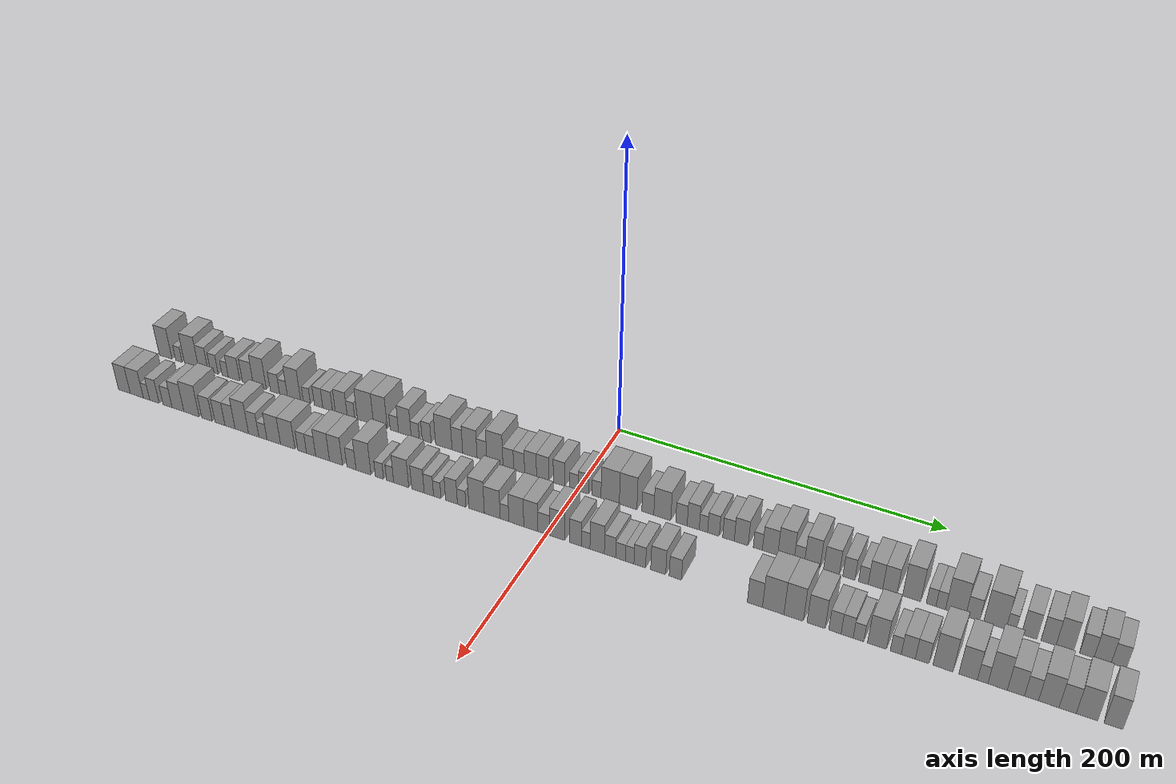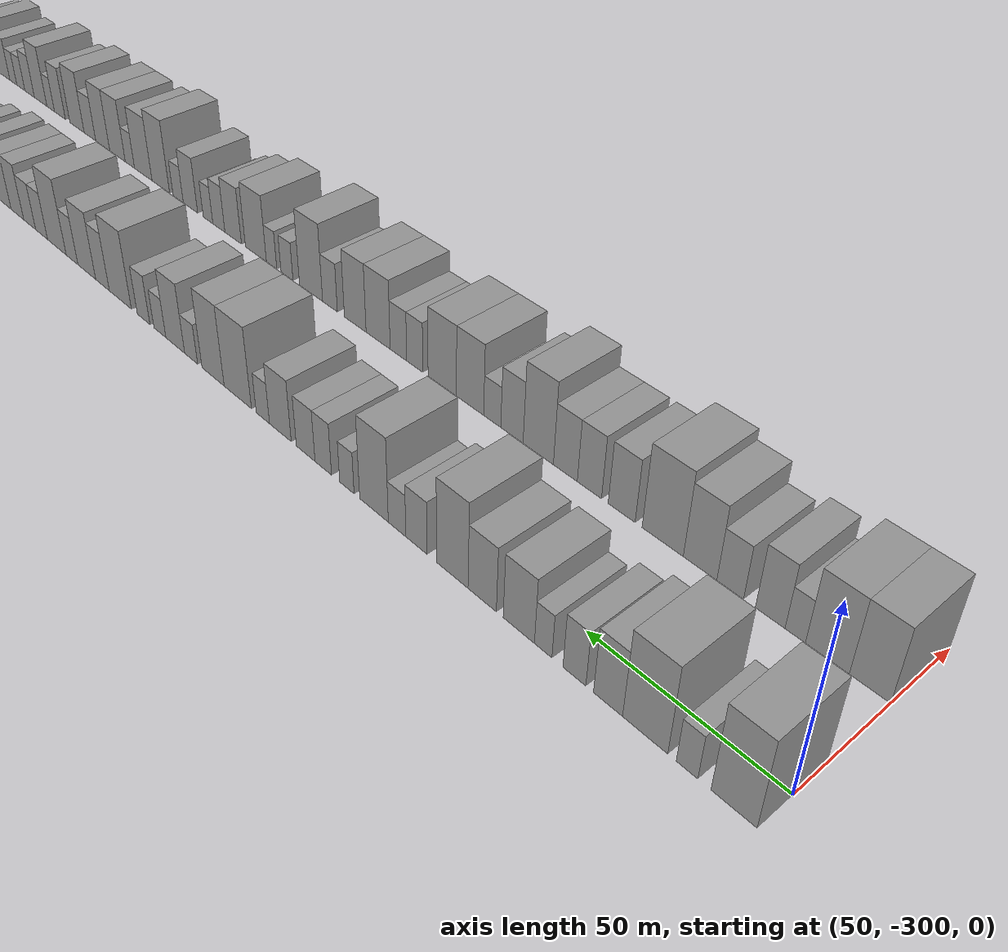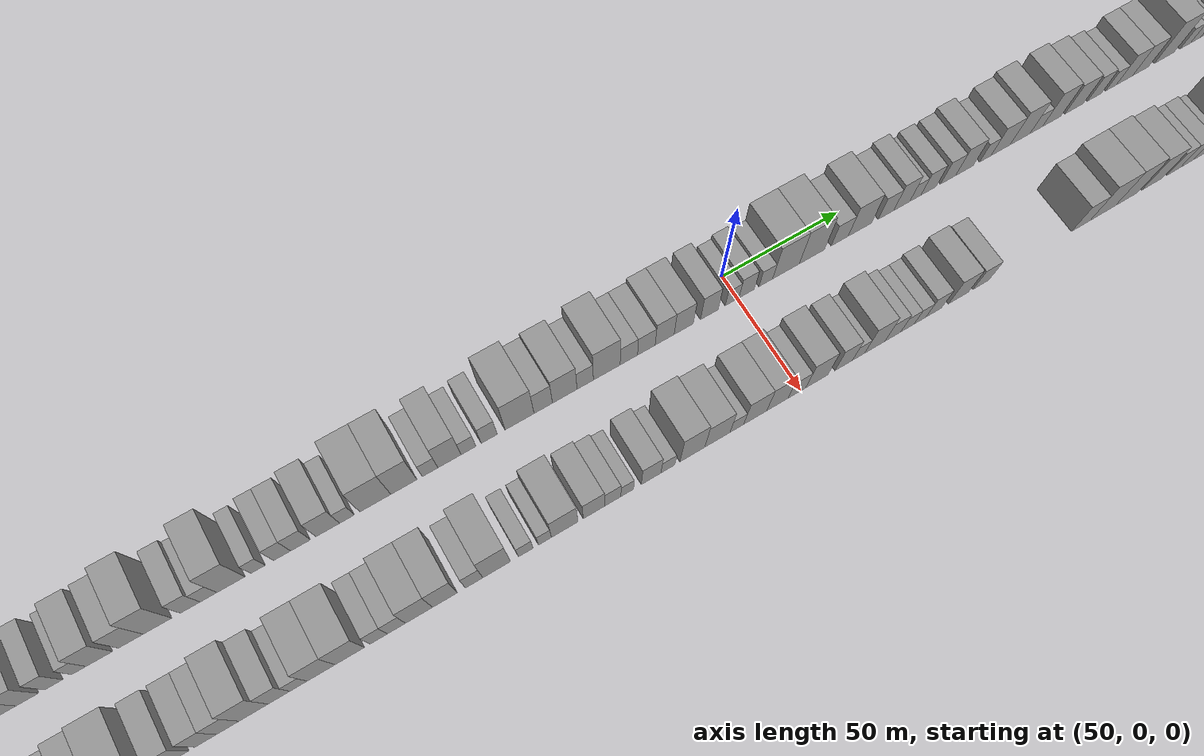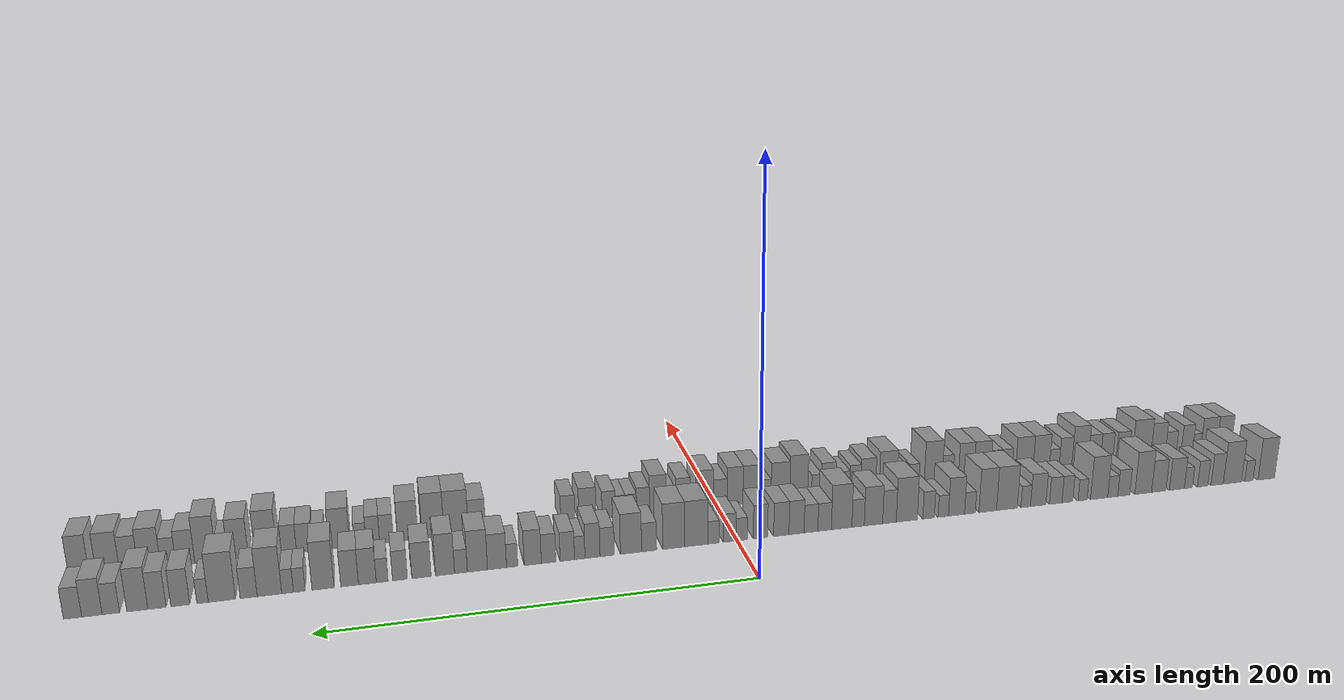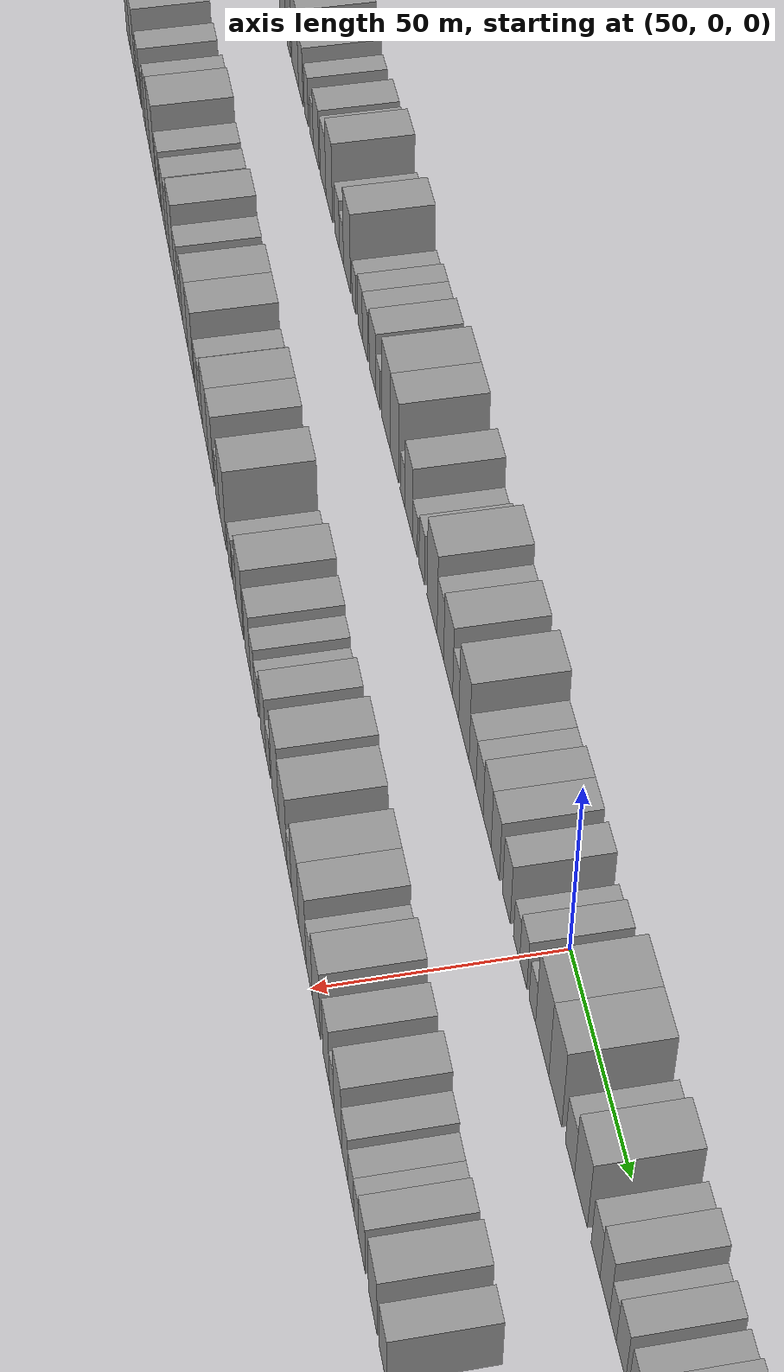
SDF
<sdf version="1.6">
 <world name="default">
  <scene>
   <sky><clouds><speed>12</speed></clouds></sky>
   <ambient>0.4 0.4 0.4 1</ambient>
   <background>0.7 0.7 0.7 1</background>
   <shadows>1</shadows>
  </scene>
  <gravity>0 0 -9.8066</gravity>
  <magnetic_field>6e-06 2.3e-05 -4.2e-05</magnetic_field>
  <physics default="0" name="default_physics" type="ode">
   <ode>
    <solver>
     <type>quick</type>
     <iters>10</iters>
     <sor>1.0</sor>
     <use_dynamic_moi_rescaling>0</use_dynamic_moi_rescaling>
    </solver>
    <constraints>
     <cfm>0</cfm>
     <erp>0.2</erp>
     <contact_max_correcting_vel>100</contact_max_correcting_vel>
     <contact_surface_layer>0.001</contact_surface_layer>
    </constraints>
   </ode>
   <max_step_size>0.004</max_step_size>
   <real_time_factor>1</real_time_factor>
   <real_time_update_rate>250</real_time_update_rate>
  </physics>
  <light name="sun" type="directional">
   <pose>0 0 10 0 0 0</pose>
   <diffuse>0.8 0.8 0.8 1</diffuse>
   <specular>0.2 0.2 0.2 1</specular>
   <attenuation>
    <range>1000</range>
    <constant>0.9</constant>
    <linear>0.01</linear>
    <quadratic>0.001</quadratic>
   </attenuation>
   <direction>-0.5 0.1 -0.9</direction>
  </light>
  <model name="building_1">
   <static>1</static>
   <pose>50.0000 -294.9108 0 0.000000 0.000000 0.000000</pose>
   <link name="link">
    <pose>0 0 12.00 0 0 0</pose>
    <collision name="collision"><geometry><box><size>20.0000 10.1784 24.0000</size></box></geometry></collision>
    <visual name="visual">
     <cast_shadows>0</cast_shadows>
     <geometry><box><size>20.0000 10.1784 24.0000</size></box></geometry>
     <material>
      <script>
       <uri>model://grey_wall/materials/scripts</uri>
       <uri>model://grey_wall/materials/textures</uri>
       <name>vrc/grey_wall</name>
      </script>
     </material>
    </visual>
   </link>
  </model>
  <model name="building_2">
   <static>1</static>
   <pose>50.0000 -284.3145 0 0.000000 0.000000 0.000000</pose>
   <link name="link">
    <pose>0 0 6.00 0 0 0</pose>
    <collision name="collision"><geometry><box><size>20.0000 5.0142 12.0000</size></box></geometry></collision>
    <visual name="visual">
     <cast_shadows>0</cast_shadows>
     <geometry><box><size>20.0000 5.0142 12.0000</size></box></geometry>
     <material>
      <script>
       <uri>model://grey_wall/materials/scripts</uri>
       <uri>model://grey_wall/materials/textures</uri>
       <name>vrc/grey_wall</name>
      </script>
     </material>
    </visual>
   </link>
  </model>
  <model name="building_3">
   <static>1</static>
   <pose>50.0000 -274.2825 0 0.000000 0.000000 0.000000</pose>
   <link name="link">
    <pose>0 0 12.00 0 0 0</pose>
    <collision name="collision"><geometry><box><size>20.0000 11.0498 24.0000</size></box></geometry></collision>
    <visual name="visual">
     <cast_shadows>0</cast_shadows>
     <geometry><box><size>20.0000 11.0498 24.0000</size></box></geometry>
     <material>
      <script>
       <uri>model://grey_wall/materials/scripts</uri>
       <uri>model://grey_wall/materials/textures</uri>
       <name>vrc/grey_wall</name>
      </script>
     </material>
    </visual>
   </link>
  </model>
  <model name="building_4">
   <static>1</static>
   <pose>50.0000 -265.0465 0 0.000000 0.000000 0.000000</pose>
   <link name="link">
    <pose>0 0 9.00 0 0 0</pose>
    <collision name="collision"><geometry><box><size>20.0000 7.4221 18.0000</size></box></geometry></collision>
    <visual name="visual">
     <cast_shadows>0</cast_shadows>
     <geometry><box><size>20.0000 7.4221 18.0000</size></box></geometry>
     <material>
      <script>
       <uri>model://grey_wall/materials/scripts</uri>
       <uri>model://grey_wall/materials/textures</uri>
       <name>vrc/grey_wall</name>
      </script>
     </material>
    </visual>
   </link>
  </model>
  <model name="building_5">
   <static>1</static>
   <pose>50.0000 -256.2958 0 0.000000 0.000000 0.000000</pose>
   <link name="link">
    <pose>0 0 7.50 0 0 0</pose>
    <collision name="collision"><geometry><box><size>20.0000 6.0794 15.0000</size></box></geometry></collision>
    <visual name="visual">
     <cast_shadows>0</cast_shadows>
     <geometry><box><size>20.0000 6.0794 15.0000</size></box></geometry>
     <material>
      <script>
       <uri>model://grey_wall/materials/scripts</uri>
       <uri>model://grey_wall/materials/textures</uri>
       <name>vrc/grey_wall</name>
      </script>
     </material>
    </visual>
   </link>
  </model>
  <model name="building_6">
   <static>1</static>
   <pose>50.0000 -247.8401 0 0.000000 0.000000 0.000000</pose>
   <link name="link">
    <pose>0 0 6.00 0 0 0</pose>
    <collision name="collision"><geometry><box><size>20.0000 4.8320 12.0000</size></box></geometry></collision>
    <visual name="visual">
     <cast_shadows>0</cast_shadows>
     <geometry><box><size>20.0000 4.8320 12.0000</size></box></geometry>
     <material>
      <script>
       <uri>model://grey_wall/materials/scripts</uri>
       <uri>model://grey_wall/materials/textures</uri>
       <name>vrc/grey_wall</name>
      </script>
     </material>
    </visual>
   </link>
  </model>
  <model name="building_7">
   <static>1</static>
   <pose>50.0000 -240.9605 0 0.000000 0.000000 0.000000</pose>
   <link name="link">
    <pose>0 0 9.00 0 0 0</pose>
    <collision name="collision"><geometry><box><size>20.0000 8.9272 18.0000</size></box></geometry></collision>
    <visual name="visual">
     <cast_shadows>0</cast_shadows>
     <geometry><box><size>20.0000 8.9272 18.0000</size></box></geometry>
     <material>
      <script>
       <uri>model://grey_wall/materials/scripts</uri>
       <uri>model://grey_wall/materials/textures</uri>
       <name>vrc/grey_wall</name>
      </script>
     </material>
    </visual>
   </link>
  </model>
  <model name="building_8">
   <static>1</static>
   <pose>50.0000 -230.2648 0 0.000000 0.000000 0.000000</pose>
   <link name="link">
    <pose>0 0 9.00 0 0 0</pose>
    <collision name="collision"><geometry><box><size>20.0000 8.4643 18.0000</size></box></geometry></collision>
    <visual name="visual">
     <cast_shadows>0</cast_shadows>
     <geometry><box><size>20.0000 8.4643 18.0000</size></box></geometry>
     <material>
      <script>
       <uri>model://grey_wall/materials/scripts</uri>
       <uri>model://grey_wall/materials/textures</uri>
       <name>vrc/grey_wall</name>
      </script>
     </material>
    </visual>
   </link>
  </model>
  <model name="building_9">
   <static>1</static>
   <pose>50.0000 -221.1187 0 0.000000 0.000000 0.000000</pose>
   <link name="link">
    <pose>0 0 12.00 0 0 0</pose>
    <collision name="collision"><geometry><box><size>20.0000 9.8279 24.0000</size></box></geometry></collision>
    <visual name="visual">
     <cast_shadows>0</cast_shadows>
     <geometry><box><size>20.0000 9.8279 24.0000</size></box></geometry>
     <material>
      <script>
       <uri>model://grey_wall/materials/scripts</uri>
       <uri>model://grey_wall/materials/textures</uri>
       <name>vrc/grey_wall</name>
      </script>
     </material>
    </visual>
   </link>
  </model>
  <model name="building_10">
   <static>1</static>
   <pose>50.0000 -209.7433 0 0.000000 0.000000 0.000000</pose>
   <link name="link">
    <pose>0 0 7.50 0 0 0</pose>
    <collision name="collision"><geometry><box><size>20.0000 6.9228 15.0000</size></box></geometry></collision>
    <visual name="visual">
     <cast_shadows>0</cast_shadows>
     <geometry><box><size>20.0000 6.9228 15.0000</size></box></geometry>
     <material>
      <script>
       <uri>model://grey_wall/materials/scripts</uri>
       <uri>model://grey_wall/materials/textures</uri>
       <name>vrc/grey_wall</name>
      </script>
     </material>
    </visual>
   </link>
  </model>
  <model name="building_11">
   <static>1</static>
   <pose>50.0000 -203.3364 0 0.000000 0.000000 0.000000</pose>
   <link name="link">
    <pose>0 0 6.00 0 0 0</pose>
    <collision name="collision"><geometry><box><size>20.0000 5.8911 12.0000</size></box></geometry></collision>
    <visual name="visual">
     <cast_shadows>0</cast_shadows>
     <geometry><box><size>20.0000 5.8911 12.0000</size></box></geometry>
     <material>
      <script>
       <uri>model://grey_wall/materials/scripts</uri>
       <uri>model://grey_wall/materials/textures</uri>
       <name>vrc/grey_wall</name>
      </script>
     </material>
    </visual>
   </link>
  </model>
  <model name="building_12">
   <static>1</static>
   <pose>50.0000 -195.4304 0 0.000000 0.000000 0.000000</pose>
   <link name="link">
    <pose>0 0 12.00 0 0 0</pose>
    <collision name="collision"><geometry><box><size>20.0000 9.9209 24.0000</size></box></geometry></collision>
    <visual name="visual">
     <cast_shadows>0</cast_shadows>
     <geometry><box><size>20.0000 9.9209 24.0000</size></box></geometry>
     <material>
      <script>
       <uri>model://grey_wall/materials/scripts</uri>
       <uri>model://grey_wall/materials/textures</uri>
       <name>vrc/grey_wall</name>
      </script>
     </material>
    </visual>
   </link>
  </model>
  <model name="building_13">
   <static>1</static>
   <pose>50.0000 -185.8845 0 0.000000 0.000000 0.000000</pose>
   <link name="link">
    <pose>0 0 6.00 0 0 0</pose>
    <collision name="collision"><geometry><box><size>20.0000 5.1708 12.0000</size></box></geometry></collision>
    <visual name="visual">
     <cast_shadows>0</cast_shadows>
     <geometry><box><size>20.0000 5.1708 12.0000</size></box></geometry>
     <material>
      <script>
       <uri>model://grey_wall/materials/scripts</uri>
       <uri>model://grey_wall/materials/textures</uri>
       <name>vrc/grey_wall</name>
      </script>
     </material>
    </visual>
   </link>
  </model>
  <model name="building_14">
   <static>1</static>
   <pose>50.0000 -177.2274 0 0.000000 0.000000 0.000000</pose>
   <link name="link">
    <pose>0 0 7.50 0 0 0</pose>
    <collision name="collision"><geometry><box><size>20.0000 6.1435 15.0000</size></box></geometry></collision>
    <visual name="visual">
     <cast_shadows>0</cast_shadows>
     <geometry><box><size>20.0000 6.1435 15.0000</size></box></geometry>
     <material>
      <script>
       <uri>model://grey_wall/materials/scripts</uri>
       <uri>model://grey_wall/materials/textures</uri>
       <name>vrc/grey_wall</name>
      </script>
     </material>
    </visual>
   </link>
  </model>
  <model name="building_15">
   <static>1</static>
   <pose>50.0000 -170.5829 0 0.000000 0.000000 0.000000</pose>
   <link name="link">
    <pose>0 0 7.50 0 0 0</pose>
    <collision name="collision"><geometry><box><size>20.0000 7.1455 15.0000</size></box></geometry></collision>
    <visual name="visual">
     <cast_shadows>0</cast_shadows>
     <geometry><box><size>20.0000 7.1455 15.0000</size></box></geometry>
     <material>
      <script>
       <uri>model://grey_wall/materials/scripts</uri>
       <uri>model://grey_wall/materials/textures</uri>
       <name>vrc/grey_wall</name>
      </script>
     </material>
    </visual>
   </link>
  </model>
  <model name="building_16">
   <static>1</static>
   <pose>50.0000 -160.6937 0 0.000000 0.000000 0.000000</pose>
   <link name="link">
    <pose>0 0 9.00 0 0 0</pose>
    <collision name="collision"><geometry><box><size>20.0000 8.6328 18.0000</size></box></geometry></collision>
    <visual name="visual">
     <cast_shadows>0</cast_shadows>
     <geometry><box><size>20.0000 8.6328 18.0000</size></box></geometry>
     <material>
      <script>
       <uri>model://grey_wall/materials/scripts</uri>
       <uri>model://grey_wall/materials/textures</uri>
       <name>vrc/grey_wall</name>
      </script>
     </material>
    </visual>
   </link>
  </model>
  <model name="building_17">
   <static>1</static>
   <pose>50.0000 -153.6714 0 0.000000 0.000000 0.000000</pose>
   <link name="link">
    <pose>0 0 6.00 0 0 0</pose>
    <collision name="collision"><geometry><box><size>20.0000 5.4120 12.0000</size></box></geometry></collision>
    <visual name="visual">
     <cast_shadows>0</cast_shadows>
     <geometry><box><size>20.0000 5.4120 12.0000</size></box></geometry>
     <material>
      <script>
       <uri>model://grey_wall/materials/scripts</uri>
       <uri>model://grey_wall/materials/textures</uri>
       <name>vrc/grey_wall</name>
      </script>
     </material>
    </visual>
   </link>
  </model>
  <model name="building_18">
   <static>1</static>
   <pose>50.0000 -143.1797 0 0.000000 0.000000 0.000000</pose>
   <link name="link">
    <pose>0 0 12.00 0 0 0</pose>
    <collision name="collision"><geometry><box><size>20.0000 11.5714 24.0000</size></box></geometry></collision>
    <visual name="visual">
     <cast_shadows>0</cast_shadows>
     <geometry><box><size>20.0000 11.5714 24.0000</size></box></geometry>
     <material>
      <script>
       <uri>model://grey_wall/materials/scripts</uri>
       <uri>model://grey_wall/materials/textures</uri>
       <name>vrc/grey_wall</name>
      </script>
     </material>
    </visual>
   </link>
  </model>
  <model name="building_19">
   <static>1</static>
   <pose>50.0000 -132.5070 0 0.000000 0.000000 0.000000</pose>
   <link name="link">
    <pose>0 0 12.00 0 0 0</pose>
    <collision name="collision"><geometry><box><size>20.0000 9.7740 24.0000</size></box></geometry></collision>
    <visual name="visual">
     <cast_shadows>0</cast_shadows>
     <geometry><box><size>20.0000 9.7740 24.0000</size></box></geometry>
     <material>
      <script>
       <uri>model://grey_wall/materials/scripts</uri>
       <uri>model://grey_wall/materials/textures</uri>
       <name>vrc/grey_wall</name>
      </script>
     </material>
    </visual>
   </link>
  </model>
  <model name="building_20">
   <static>1</static>
   <pose>50.0000 -122.6663 0 0.000000 0.000000 0.000000</pose>
   <link name="link">
    <pose>0 0 6.00 0 0 0</pose>
    <collision name="collision"><geometry><box><size>20.0000 5.9075 12.0000</size></box></geometry></collision>
    <visual name="visual">
     <cast_shadows>0</cast_shadows>
     <geometry><box><size>20.0000 5.9075 12.0000</size></box></geometry>
     <material>
      <script>
       <uri>model://grey_wall/materials/scripts</uri>
       <uri>model://grey_wall/materials/textures</uri>
       <name>vrc/grey_wall</name>
      </script>
     </material>
    </visual>
   </link>
  </model>
  <model name="building_21">
   <static>1</static>
   <pose>50.0000 -115.2977 0 0.000000 0.000000 0.000000</pose>
   <link name="link">
    <pose>0 0 10.50 0 0 0</pose>
    <collision name="collision"><geometry><box><size>20.0000 8.8297 21.0000</size></box></geometry></collision>
    <visual name="visual">
     <cast_shadows>0</cast_shadows>
     <geometry><box><size>20.0000 8.8297 21.0000</size></box></geometry>
     <material>
      <script>
       <uri>model://grey_wall/materials/scripts</uri>
       <uri>model://grey_wall/materials/textures</uri>
       <name>vrc/grey_wall</name>
      </script>
     </material>
    </visual>
   </link>
  </model>
  <model name="building_22">
   <static>1</static>
   <pose>50.0000 -108.0368 0 0.000000 0.000000 0.000000</pose>
   <link name="link">
    <pose>0 0 6.00 0 0 0</pose>
    <collision name="collision"><geometry><box><size>20.0000 5.6920 12.0000</size></box></geometry></collision>
    <visual name="visual">
     <cast_shadows>0</cast_shadows>
     <geometry><box><size>20.0000 5.6920 12.0000</size></box></geometry>
     <material>
      <script>
       <uri>model://grey_wall/materials/scripts</uri>
       <uri>model://grey_wall/materials/textures</uri>
       <name>vrc/grey_wall</name>
      </script>
     </material>
    </visual>
   </link>
  </model>
  <model name="building_23">
   <static>1</static>
   <pose>50.0000 -100.0813 0 0.000000 0.000000 0.000000</pose>
   <link name="link">
    <pose>0 0 7.50 0 0 0</pose>
    <collision name="collision"><geometry><box><size>20.0000 6.2189 15.0000</size></box></geometry></collision>
    <visual name="visual">
     <cast_shadows>0</cast_shadows>
     <geometry><box><size>20.0000 6.2189 15.0000</size></box></geometry>
     <material>
      <script>
       <uri>model://grey_wall/materials/scripts</uri>
       <uri>model://grey_wall/materials/textures</uri>
       <name>vrc/grey_wall</name>
      </script>
     </material>
    </visual>
   </link>
  </model>
  <model name="building_24">
   <static>1</static>
   <pose>50.0000 -88.3045 0 0.000000 0.000000 0.000000</pose>
   <link name="link">
    <pose>0 0 12.00 0 0 0</pose>
    <collision name="collision"><geometry><box><size>20.0000 11.3347 24.0000</size></box></geometry></collision>
    <visual name="visual">
     <cast_shadows>0</cast_shadows>
     <geometry><box><size>20.0000 11.3347 24.0000</size></box></geometry>
     <material>
      <script>
       <uri>model://grey_wall/materials/scripts</uri>
       <uri>model://grey_wall/materials/textures</uri>
       <name>vrc/grey_wall</name>
      </script>
     </material>
    </visual>
   </link>
  </model>
  <model name="building_25">
   <static>1</static>
   <pose>50.0000 -79.0158 0 0.000000 0.000000 0.000000</pose>
   <link name="link">
    <pose>0 0 9.00 0 0 0</pose>
    <collision name="collision"><geometry><box><size>20.0000 7.2427 18.0000</size></box></geometry></collision>
    <visual name="visual">
     <cast_shadows>0</cast_shadows>
     <geometry><box><size>20.0000 7.2427 18.0000</size></box></geometry>
     <material>
      <script>
       <uri>model://grey_wall/materials/scripts</uri>
       <uri>model://grey_wall/materials/textures</uri>
       <name>vrc/grey_wall</name>
      </script>
     </material>
    </visual>
   </link>
  </model>
  <model name="building_26">
   <static>1</static>
   <pose>50.0000 -70.5292 0 0.000000 0.000000 0.000000</pose>
   <link name="link">
    <pose>0 0 10.50 0 0 0</pose>
    <collision name="collision"><geometry><box><size>20.0000 9.7304 21.0000</size></box></geometry></collision>
    <visual name="visual">
     <cast_shadows>0</cast_shadows>
     <geometry><box><size>20.0000 9.7304 21.0000</size></box></geometry>
     <material>
      <script>
       <uri>model://grey_wall/materials/scripts</uri>
       <uri>model://grey_wall/materials/textures</uri>
       <name>vrc/grey_wall</name>
      </script>
     </material>
    </visual>
   </link>
  </model>
  <model name="building_27">
   <static>1</static>
   <pose>50.0000 -62.3960 0 0.000000 0.000000 0.000000</pose>
   <link name="link">
    <pose>0 0 7.50 0 0 0</pose>
    <collision name="collision"><geometry><box><size>20.0000 6.5360 15.0000</size></box></geometry></collision>
    <visual name="visual">
     <cast_shadows>0</cast_shadows>
     <geometry><box><size>20.0000 6.5360 15.0000</size></box></geometry>
     <material>
      <script>
       <uri>model://grey_wall/materials/scripts</uri>
       <uri>model://grey_wall/materials/textures</uri>
       <name>vrc/grey_wall</name>
      </script>
     </material>
    </visual>
   </link>
  </model>
  <model name="building_28">
   <static>1</static>
   <pose>50.0000 -53.7417 0 0.000000 0.000000 0.000000</pose>
   <link name="link">
    <pose>0 0 12.00 0 0 0</pose>
    <collision name="collision"><geometry><box><size>20.0000 10.7727 24.0000</size></box></geometry></collision>
    <visual name="visual">
     <cast_shadows>0</cast_shadows>
     <geometry><box><size>20.0000 10.7727 24.0000</size></box></geometry>
     <material>
      <script>
       <uri>model://grey_wall/materials/scripts</uri>
       <uri>model://grey_wall/materials/textures</uri>
       <name>vrc/grey_wall</name>
      </script>
     </material>
    </visual>
   </link>
  </model>
  <model name="building_29">
   <static>1</static>
   <pose>50.0000 -44.8330 0 0.000000 0.000000 0.000000</pose>
   <link name="link">
    <pose>0 0 7.50 0 0 0</pose>
    <collision name="collision"><geometry><box><size>20.0000 7.0446 15.0000</size></box></geometry></collision>
    <visual name="visual">
     <cast_shadows>0</cast_shadows>
     <geometry><box><size>20.0000 7.0446 15.0000</size></box></geometry>
     <material>
      <script>
       <uri>model://grey_wall/materials/scripts</uri>
       <uri>model://grey_wall/materials/textures</uri>
       <name>vrc/grey_wall</name>
      </script>
     </material>
    </visual>
   </link>
  </model>
  <model name="building_30">
   <static>1</static>
   <pose>50.0000 -37.7096 0 0.000000 0.000000 0.000000</pose>
   <link name="link">
    <pose>0 0 7.50 0 0 0</pose>
    <collision name="collision"><geometry><box><size>20.0000 7.2022 15.0000</size></box></geometry></collision>
    <visual name="visual">
     <cast_shadows>0</cast_shadows>
     <geometry><box><size>20.0000 7.2022 15.0000</size></box></geometry>
     <material>
      <script>
       <uri>model://grey_wall/materials/scripts</uri>
       <uri>model://grey_wall/materials/textures</uri>
       <name>vrc/grey_wall</name>
      </script>
     </material>
    </visual>
   </link>
  </model>
  <model name="building_31">
   <static>1</static>
   <pose>50.0000 -30.2062 0 0.000000 0.000000 0.000000</pose>
   <link name="link">
    <pose>0 0 9.00 0 0 0</pose>
    <collision name="collision"><geometry><box><size>20.0000 7.8048 18.0000</size></box></geometry></collision>
    <visual name="visual">
     <cast_shadows>0</cast_shadows>
     <geometry><box><size>20.0000 7.8048 18.0000</size></box></geometry>
     <material>
      <script>
       <uri>model://grey_wall/materials/scripts</uri>
       <uri>model://grey_wall/materials/textures</uri>
       <name>vrc/grey_wall</name>
      </script>
     </material>
    </visual>
   </link>
  </model>
  <model name="building_32">
   <static>1</static>
   <pose>50.0000 -22.3476 0 0.000000 0.000000 0.000000</pose>
   <link name="link">
    <pose>0 0 9.00 0 0 0</pose>
    <collision name="collision"><geometry><box><size>20.0000 7.9123 18.0000</size></box></geometry></collision>
    <visual name="visual">
     <cast_shadows>0</cast_shadows>
     <geometry><box><size>20.0000 7.9123 18.0000</size></box></geometry>
     <material>
      <script>
       <uri>model://grey_wall/materials/scripts</uri>
       <uri>model://grey_wall/materials/textures</uri>
       <name>vrc/grey_wall</name>
      </script>
     </material>
    </visual>
   </link>
  </model>
  <model name="building_33">
   <static>1</static>
   <pose>50.0000 -11.7090 0 0.000000 0.000000 0.000000</pose>
   <link name="link">
    <pose>0 0 9.00 0 0 0</pose>
    <collision name="collision"><geometry><box><size>20.0000 7.3649 18.0000</size></box></geometry></collision>
    <visual name="visual">
     <cast_shadows>0</cast_shadows>
     <geometry><box><size>20.0000 7.3649 18.0000</size></box></geometry>
     <material>
      <script>
       <uri>model://grey_wall/materials/scripts</uri>
       <uri>model://grey_wall/materials/textures</uri>
       <name>vrc/grey_wall</name>
      </script>
     </material>
    </visual>
   </link>
  </model>
  <model name="building_34">
   <static>1</static>
   <pose>50.0000 -2.1752 0 0.000000 0.000000 0.000000</pose>
   <link name="link">
    <pose>0 0 6.00 0 0 0</pose>
    <collision name="collision"><geometry><box><size>20.0000 5.7027 12.0000</size></box></geometry></collision>
    <visual name="visual">
     <cast_shadows>0</cast_shadows>
     <geometry><box><size>20.0000 5.7027 12.0000</size></box></geometry>
     <material>
      <script>
       <uri>model://grey_wall/materials/scripts</uri>
       <uri>model://grey_wall/materials/textures</uri>
       <name>vrc/grey_wall</name>
      </script>
     </material>
    </visual>
   </link>
  </model>
  <model name="building_35">
   <static>1</static>
   <pose>50.0000 3.9535 0 0.000000 0.000000 0.000000</pose>
   <link name="link">
    <pose>0 0 7.50 0 0 0</pose>
    <collision name="collision"><geometry><box><size>20.0000 6.5547 15.0000</size></box></geometry></collision>
    <visual name="visual">
     <cast_shadows>0</cast_shadows>
     <geometry><box><size>20.0000 6.5547 15.0000</size></box></geometry>
     <material>
      <script>
       <uri>model://grey_wall/materials/scripts</uri>
       <uri>model://grey_wall/materials/textures</uri>
       <name>vrc/grey_wall</name>
      </script>
     </material>
    </visual>
   </link>
  </model>
  <model name="building_36">
   <static>1</static>
   <pose>50.0000 12.1272 0 0.000000 0.000000 0.000000</pose>
   <link name="link">
    <pose>0 0 6.00 0 0 0</pose>
    <collision name="collision"><geometry><box><size>20.0000 5.7927 12.0000</size></box></geometry></collision>
    <visual name="visual">
     <cast_shadows>0</cast_shadows>
     <geometry><box><size>20.0000 5.7927 12.0000</size></box></geometry>
     <material>
      <script>
       <uri>model://grey_wall/materials/scripts</uri>
       <uri>model://grey_wall/materials/textures</uri>
       <name>vrc/grey_wall</name>
      </script>
     </material>
    </visual>
   </link>
  </model>
  <model name="building_37">
   <static>1</static>
   <pose>50.0000 20.7689 0 0.000000 0.000000 0.000000</pose>
   <link name="link">
    <pose>0 0 12.00 0 0 0</pose>
    <collision name="collision"><geometry><box><size>20.0000 11.4906 24.0000</size></box></geometry></collision>
    <visual name="visual">
     <cast_shadows>0</cast_shadows>
     <geometry><box><size>20.0000 11.4906 24.0000</size></box></geometry>
     <material>
      <script>
       <uri>model://grey_wall/materials/scripts</uri>
       <uri>model://grey_wall/materials/textures</uri>
       <name>vrc/grey_wall</name>
      </script>
     </material>
    </visual>
   </link>
  </model>
  <model name="building_38">
   <static>1</static>
   <pose>50.0000 31.9751 0 0.000000 0.000000 0.000000</pose>
   <link name="link">
    <pose>0 0 12.00 0 0 0</pose>
    <collision name="collision"><geometry><box><size>20.0000 10.9218 24.0000</size></box></geometry></collision>
    <visual name="visual">
     <cast_shadows>0</cast_shadows>
     <geometry><box><size>20.0000 10.9218 24.0000</size></box></geometry>
     <material>
      <script>
       <uri>model://grey_wall/materials/scripts</uri>
       <uri>model://grey_wall/materials/textures</uri>
       <name>vrc/grey_wall</name>
      </script>
     </material>
    </visual>
   </link>
  </model>
  <model name="building_39">
   <static>1</static>
   <pose>50.0000 44.1195 0 0.000000 0.000000 0.000000</pose>
   <link name="link">
    <pose>0 0 7.50 0 0 0</pose>
    <collision name="collision"><geometry><box><size>20.0000 7.3670 15.0000</size></box></geometry></collision>
    <visual name="visual">
     <cast_shadows>0</cast_shadows>
     <geometry><box><size>20.0000 7.3670 15.0000</size></box></geometry>
     <material>
      <script>
       <uri>model://grey_wall/materials/scripts</uri>
       <uri>model://grey_wall/materials/textures</uri>
       <name>vrc/grey_wall</name>
      </script>
     </material>
    </visual>
   </link>
  </model>
  <model name="building_40">
   <static>1</static>
   <pose>50.0000 52.9714 0 0.000000 0.000000 0.000000</pose>
   <link name="link">
    <pose>0 0 10.50 0 0 0</pose>
    <collision name="collision"><geometry><box><size>20.0000 10.3369 21.0000</size></box></geometry></collision>
    <visual name="visual">
     <cast_shadows>0</cast_shadows>
     <geometry><box><size>20.0000 10.3369 21.0000</size></box></geometry>
     <material>
      <script>
       <uri>model://grey_wall/materials/scripts</uri>
       <uri>model://grey_wall/materials/textures</uri>
       <name>vrc/grey_wall</name>
      </script>
     </material>
    </visual>
   </link>
  </model>
  <model name="building_41">
   <static>1</static>
   <pose>50.0000 64.5912 0 0.000000 0.000000 0.000000</pose>
   <link name="link">
    <pose>0 0 7.50 0 0 0</pose>
    <collision name="collision"><geometry><box><size>20.0000 6.9026 15.0000</size></box></geometry></collision>
    <visual name="visual">
     <cast_shadows>0</cast_shadows>
     <geometry><box><size>20.0000 6.9026 15.0000</size></box></geometry>
     <material>
      <script>
       <uri>model://grey_wall/materials/scripts</uri>
       <uri>model://grey_wall/materials/textures</uri>
       <name>vrc/grey_wall</name>
      </script>
     </material>
    </visual>
   </link>
  </model>
  <model name="building_42">
   <static>1</static>
   <pose>50.0000 71.6783 0 0.000000 0.000000 0.000000</pose>
   <link name="link">
    <pose>0 0 9.00 0 0 0</pose>
    <collision name="collision"><geometry><box><size>20.0000 7.2717 18.0000</size></box></geometry></collision>
    <visual name="visual">
     <cast_shadows>0</cast_shadows>
     <geometry><box><size>20.0000 7.2717 18.0000</size></box></geometry>
     <material>
      <script>
       <uri>model://grey_wall/materials/scripts</uri>
       <uri>model://grey_wall/materials/textures</uri>
       <name>vrc/grey_wall</name>
      </script>
     </material>
    </visual>
   </link>
  </model>
  <model name="building_43">
   <static>1</static>
   <pose>50.0000 77.8139 0 0.000000 0.000000 0.000000</pose>
   <link name="link">
    <pose>0 0 6.00 0 0 0</pose>
    <collision name="collision"><geometry><box><size>20.0000 4.9995 12.0000</size></box></geometry></collision>
    <visual name="visual">
     <cast_shadows>0</cast_shadows>
     <geometry><box><size>20.0000 4.9995 12.0000</size></box></geometry>
     <material>
      <script>
       <uri>model://grey_wall/materials/scripts</uri>
       <uri>model://grey_wall/materials/textures</uri>
       <name>vrc/grey_wall</name>
      </script>
     </material>
    </visual>
   </link>
  </model>
  <model name="building_44">
   <static>1</static>
   <pose>50.0000 83.7802 0 0.000000 0.000000 0.000000</pose>
   <link name="link">
    <pose>0 0 7.50 0 0 0</pose>
    <collision name="collision"><geometry><box><size>20.0000 6.9331 15.0000</size></box></geometry></collision>
    <visual name="visual">
     <cast_shadows>0</cast_shadows>
     <geometry><box><size>20.0000 6.9331 15.0000</size></box></geometry>
     <material>
      <script>
       <uri>model://grey_wall/materials/scripts</uri>
       <uri>model://grey_wall/materials/textures</uri>
       <name>vrc/grey_wall</name>
      </script>
     </material>
    </visual>
   </link>
  </model>
  <model name="building_45">
   <static>1</static>
   <pose>50.0000 92.6719 0 0.000000 0.000000 0.000000</pose>
   <link name="link">
    <pose>0 0 7.50 0 0 0</pose>
    <collision name="collision"><geometry><box><size>20.0000 6.8504 15.0000</size></box></geometry></collision>
    <visual name="visual">
     <cast_shadows>0</cast_shadows>
     <geometry><box><size>20.0000 6.8504 15.0000</size></box></geometry>
     <material>
      <script>
       <uri>model://grey_wall/materials/scripts</uri>
       <uri>model://grey_wall/materials/textures</uri>
       <name>vrc/grey_wall</name>
      </script>
     </material>
    </visual>
   </link>
  </model>
  <model name="building_46">
   <static>1</static>
   <pose>50.0000 100.1670 0 0.000000 0.000000 0.000000</pose>
   <link name="link">
    <pose>0 0 9.00 0 0 0</pose>
    <collision name="collision"><geometry><box><size>20.0000 8.1397 18.0000</size></box></geometry></collision>
    <visual name="visual">
     <cast_shadows>0</cast_shadows>
     <geometry><box><size>20.0000 8.1397 18.0000</size></box></geometry>
     <material>
      <script>
       <uri>model://grey_wall/materials/scripts</uri>
       <uri>model://grey_wall/materials/textures</uri>
       <name>vrc/grey_wall</name>
      </script>
     </material>
    </visual>
   </link>
  </model>
  <model name="building_47">
   <static>1</static>
   <pose>50.0000 109.8705 0 0.000000 0.000000 0.000000</pose>
   <link name="link">
    <pose>0 0 6.00 0 0 0</pose>
    <collision name="collision"><geometry><box><size>20.0000 5.2673 12.0000</size></box></geometry></collision>
    <visual name="visual">
     <cast_shadows>0</cast_shadows>
     <geometry><box><size>20.0000 5.2673 12.0000</size></box></geometry>
     <material>
      <script>
       <uri>model://grey_wall/materials/scripts</uri>
       <uri>model://grey_wall/materials/textures</uri>
       <name>vrc/grey_wall</name>
      </script>
     </material>
    </visual>
   </link>
  </model>
  <model name="building_48">
   <static>1</static>
   <pose>50.0000 116.9437 0 0.000000 0.000000 0.000000</pose>
   <link name="link">
    <pose>0 0 9.00 0 0 0</pose>
    <collision name="collision"><geometry><box><size>20.0000 8.8791 18.0000</size></box></geometry></collision>
    <visual name="visual">
     <cast_shadows>0</cast_shadows>
     <geometry><box><size>20.0000 8.8791 18.0000</size></box></geometry>
     <material>
      <script>
       <uri>model://grey_wall/materials/scripts</uri>
       <uri>model://grey_wall/materials/textures</uri>
       <name>vrc/grey_wall</name>
      </script>
     </material>
    </visual>
   </link>
  </model>
  <model name="building_49">
   <static>1</static>
   <pose>50.0000 126.0535 0 0.000000 0.000000 0.000000</pose>
   <link name="link">
    <pose>0 0 10.50 0 0 0</pose>
    <collision name="collision"><geometry><box><size>20.0000 9.3406 21.0000</size></box></geometry></collision>
    <visual name="visual">
     <cast_shadows>0</cast_shadows>
     <geometry><box><size>20.0000 9.3406 21.0000</size></box></geometry>
     <material>
      <script>
       <uri>model://grey_wall/materials/scripts</uri>
       <uri>model://grey_wall/materials/textures</uri>
       <name>vrc/grey_wall</name>
      </script>
     </material>
    </visual>
   </link>
  </model>
  <model name="building_50">
   <static>1</static>
   <pose>50.0000 133.6746 0 0.000000 0.000000 0.000000</pose>
   <link name="link">
    <pose>0 0 6.00 0 0 0</pose>
    <collision name="collision"><geometry><box><size>20.0000 5.9016 12.0000</size></box></geometry></collision>
    <visual name="visual">
     <cast_shadows>0</cast_shadows>
     <geometry><box><size>20.0000 5.9016 12.0000</size></box></geometry>
     <material>
      <script>
       <uri>model://grey_wall/materials/scripts</uri>
       <uri>model://grey_wall/materials/textures</uri>
       <name>vrc/grey_wall</name>
      </script>
     </material>
    </visual>
   </link>
  </model>
  <model name="building_51">
   <static>1</static>
   <pose>50.0000 140.9963 0 0.000000 0.000000 0.000000</pose>
   <link name="link">
    <pose>0 0 10.50 0 0 0</pose>
    <collision name="collision"><geometry><box><size>20.0000 8.7419 21.0000</size></box></geometry></collision>
    <visual name="visual">
     <cast_shadows>0</cast_shadows>
     <geometry><box><size>20.0000 8.7419 21.0000</size></box></geometry>
     <material>
      <script>
       <uri>model://grey_wall/materials/scripts</uri>
       <uri>model://grey_wall/materials/textures</uri>
       <name>vrc/grey_wall</name>
      </script>
     </material>
    </visual>
   </link>
  </model>
  <model name="building_52">
   <static>1</static>
   <pose>50.0000 151.7651 0 0.000000 0.000000 0.000000</pose>
   <link name="link">
    <pose>0 0 9.00 0 0 0</pose>
    <collision name="collision"><geometry><box><size>20.0000 8.7956 18.0000</size></box></geometry></collision>
    <visual name="visual">
     <cast_shadows>0</cast_shadows>
     <geometry><box><size>20.0000 8.7956 18.0000</size></box></geometry>
     <material>
      <script>
       <uri>model://grey_wall/materials/scripts</uri>
       <uri>model://grey_wall/materials/textures</uri>
       <name>vrc/grey_wall</name>
      </script>
     </material>
    </visual>
   </link>
  </model>
  <model name="building_53">
   <static>1</static>
   <pose>50.0000 161.5239 0 0.000000 0.000000 0.000000</pose>
   <link name="link">
    <pose>0 0 7.50 0 0 0</pose>
    <collision name="collision"><geometry><box><size>20.0000 6.7221 15.0000</size></box></geometry></collision>
    <visual name="visual">
     <cast_shadows>0</cast_shadows>
     <geometry><box><size>20.0000 6.7221 15.0000</size></box></geometry>
     <material>
      <script>
       <uri>model://grey_wall/materials/scripts</uri>
       <uri>model://grey_wall/materials/textures</uri>
       <name>vrc/grey_wall</name>
      </script>
     </material>
    </visual>
   </link>
  </model>
  <model name="building_54">
   <static>1</static>
   <pose>50.0000 169.5482 0 0.000000 0.000000 0.000000</pose>
   <link name="link">
    <pose>0 0 6.00 0 0 0</pose>
    <collision name="collision"><geometry><box><size>20.0000 5.3264 12.0000</size></box></geometry></collision>
    <visual name="visual">
     <cast_shadows>0</cast_shadows>
     <geometry><box><size>20.0000 5.3264 12.0000</size></box></geometry>
     <material>
      <script>
       <uri>model://grey_wall/materials/scripts</uri>
       <uri>model://grey_wall/materials/textures</uri>
       <name>vrc/grey_wall</name>
      </script>
     </material>
    </visual>
   </link>
  </model>
  <model name="building_55">
   <static>1</static>
   <pose>50.0000 176.1844 0 0.000000 0.000000 0.000000</pose>
   <link name="link">
    <pose>0 0 9.00 0 0 0</pose>
    <collision name="collision"><geometry><box><size>20.0000 7.9460 18.0000</size></box></geometry></collision>
    <visual name="visual">
     <cast_shadows>0</cast_shadows>
     <geometry><box><size>20.0000 7.9460 18.0000</size></box></geometry>
     <material>
      <script>
       <uri>model://grey_wall/materials/scripts</uri>
       <uri>model://grey_wall/materials/textures</uri>
       <name>vrc/grey_wall</name>
      </script>
     </material>
    </visual>
   </link>
  </model>
  <model name="building_56">
   <static>1</static>
   <pose>50.0000 184.0866 0 0.000000 0.000000 0.000000</pose>
   <link name="link">
    <pose>0 0 9.00 0 0 0</pose>
    <collision name="collision"><geometry><box><size>20.0000 7.8584 18.0000</size></box></geometry></collision>
    <visual name="visual">
     <cast_shadows>0</cast_shadows>
     <geometry><box><size>20.0000 7.8584 18.0000</size></box></geometry>
     <material>
      <script>
       <uri>model://grey_wall/materials/scripts</uri>
       <uri>model://grey_wall/materials/textures</uri>
       <name>vrc/grey_wall</name>
      </script>
     </material>
    </visual>
   </link>
  </model>
  <model name="building_57">
   <static>1</static>
   <pose>50.0000 195.8710 0 0.000000 0.000000 0.000000</pose>
   <link name="link">
    <pose>0 0 12.00 0 0 0</pose>
    <collision name="collision"><geometry><box><size>20.0000 9.7103 24.0000</size></box></geometry></collision>
    <visual name="visual">
     <cast_shadows>0</cast_shadows>
     <geometry><box><size>20.0000 9.7103 24.0000</size></box></geometry>
     <material>
      <script>
       <uri>model://grey_wall/materials/scripts</uri>
       <uri>model://grey_wall/materials/textures</uri>
       <name>vrc/grey_wall</name>
      </script>
     </material>
    </visual>
   </link>
  </model>
  <model name="building_58">
   <static>1</static>
   <pose>50.0000 206.3049 0 0.000000 0.000000 0.000000</pose>
   <link name="link">
    <pose>0 0 6.00 0 0 0</pose>
    <collision name="collision"><geometry><box><size>20.0000 5.1576 12.0000</size></box></geometry></collision>
    <visual name="visual">
     <cast_shadows>0</cast_shadows>
     <geometry><box><size>20.0000 5.1576 12.0000</size></box></geometry>
     <material>
      <script>
       <uri>model://grey_wall/materials/scripts</uri>
       <uri>model://grey_wall/materials/textures</uri>
       <name>vrc/grey_wall</name>
      </script>
     </material>
    </visual>
   </link>
  </model>
  <model name="building_59">
   <static>1</static>
   <pose>50.0000 211.4171 0 0.000000 0.000000 0.000000</pose>
   <link name="link">
    <pose>0 0 6.00 0 0 0</pose>
    <collision name="collision"><geometry><box><size>20.0000 5.0667 12.0000</size></box></geometry></collision>
    <visual name="visual">
     <cast_shadows>0</cast_shadows>
     <geometry><box><size>20.0000 5.0667 12.0000</size></box></geometry>
     <material>
      <script>
       <uri>model://grey_wall/materials/scripts</uri>
       <uri>model://grey_wall/materials/textures</uri>
       <name>vrc/grey_wall</name>
      </script>
     </material>
    </visual>
   </link>
  </model>
  <model name="building_60">
   <static>1</static>
   <pose>50.0000 219.2681 0 0.000000 0.000000 0.000000</pose>
   <link name="link">
    <pose>0 0 12.00 0 0 0</pose>
    <collision name="collision"><geometry><box><size>20.0000 10.6354 24.0000</size></box></geometry></collision>
    <visual name="visual">
     <cast_shadows>0</cast_shadows>
     <geometry><box><size>20.0000 10.6354 24.0000</size></box></geometry>
     <material>
      <script>
       <uri>model://grey_wall/materials/scripts</uri>
       <uri>model://grey_wall/materials/textures</uri>
       <name>vrc/grey_wall</name>
      </script>
     </material>
    </visual>
   </link>
  </model>
  <model name="building_61">
   <static>1</static>
   <pose>50.0000 228.2614 0 0.000000 0.000000 0.000000</pose>
   <link name="link">
    <pose>0 0 7.50 0 0 0</pose>
    <collision name="collision"><geometry><box><size>20.0000 7.3512 15.0000</size></box></geometry></collision>
    <visual name="visual">
     <cast_shadows>0</cast_shadows>
     <geometry><box><size>20.0000 7.3512 15.0000</size></box></geometry>
     <material>
      <script>
       <uri>model://grey_wall/materials/scripts</uri>
       <uri>model://grey_wall/materials/textures</uri>
       <name>vrc/grey_wall</name>
      </script>
     </material>
    </visual>
   </link>
  </model>
  <model name="building_62">
   <static>1</static>
   <pose>50.0000 239.7680 0 0.000000 0.000000 0.000000</pose>
   <link name="link">
    <pose>0 0 12.00 0 0 0</pose>
    <collision name="collision"><geometry><box><size>20.0000 11.6618 24.0000</size></box></geometry></collision>
    <visual name="visual">
     <cast_shadows>0</cast_shadows>
     <geometry><box><size>20.0000 11.6618 24.0000</size></box></geometry>
     <material>
      <script>
       <uri>model://grey_wall/materials/scripts</uri>
       <uri>model://grey_wall/materials/textures</uri>
       <name>vrc/grey_wall</name>
      </script>
     </material>
    </visual>
   </link>
  </model>
  <model name="building_63">
   <static>1</static>
   <pose>50.0000 248.0155 0 0.000000 0.000000 0.000000</pose>
   <link name="link">
    <pose>0 0 6.00 0 0 0</pose>
    <collision name="collision"><geometry><box><size>20.0000 4.8333 12.0000</size></box></geometry></collision>
    <visual name="visual">
     <cast_shadows>0</cast_shadows>
     <geometry><box><size>20.0000 4.8333 12.0000</size></box></geometry>
     <material>
      <script>
       <uri>model://grey_wall/materials/scripts</uri>
       <uri>model://grey_wall/materials/textures</uri>
       <name>vrc/grey_wall</name>
      </script>
     </material>
    </visual>
   </link>
  </model>
  <model name="building_64">
   <static>1</static>
   <pose>50.0000 257.3985 0 0.000000 0.000000 0.000000</pose>
   <link name="link">
    <pose>0 0 9.00 0 0 0</pose>
    <collision name="collision"><geometry><box><size>20.0000 7.9327 18.0000</size></box></geometry></collision>
    <visual name="visual">
     <cast_shadows>0</cast_shadows>
     <geometry><box><size>20.0000 7.9327 18.0000</size></box></geometry>
     <material>
      <script>
       <uri>model://grey_wall/materials/scripts</uri>
       <uri>model://grey_wall/materials/textures</uri>
       <name>vrc/grey_wall</name>
      </script>
     </material>
    </visual>
   </link>
  </model>
  <model name="building_65">
   <static>1</static>
   <pose>50.0000 267.1753 0 0.000000 0.000000 0.000000</pose>
   <link name="link">
    <pose>0 0 9.00 0 0 0</pose>
    <collision name="collision"><geometry><box><size>20.0000 7.6208 18.0000</size></box></geometry></collision>
    <visual name="visual">
     <cast_shadows>0</cast_shadows>
     <geometry><box><size>20.0000 7.6208 18.0000</size></box></geometry>
     <material>
      <script>
       <uri>model://grey_wall/materials/scripts</uri>
       <uri>model://grey_wall/materials/textures</uri>
       <name>vrc/grey_wall</name>
      </script>
     </material>
    </visual>
   </link>
  </model>
  <model name="building_66">
   <static>1</static>
   <pose>50.0000 275.3630 0 0.000000 0.000000 0.000000</pose>
   <link name="link">
    <pose>0 0 10.50 0 0 0</pose>
    <collision name="collision"><geometry><box><size>20.0000 8.7547 21.0000</size></box></geometry></collision>
    <visual name="visual">
     <cast_shadows>0</cast_shadows>
     <geometry><box><size>20.0000 8.7547 21.0000</size></box></geometry>
     <material>
      <script>
       <uri>model://grey_wall/materials/scripts</uri>
       <uri>model://grey_wall/materials/textures</uri>
       <name>vrc/grey_wall</name>
      </script>
     </material>
    </visual>
   </link>
  </model>
  <model name="building_67">
   <static>1</static>
   <pose>50.0000 286.3343 0 0.000000 0.000000 0.000000</pose>
   <link name="link">
    <pose>0 0 7.50 0 0 0</pose>
    <collision name="collision"><geometry><box><size>20.0000 7.1880 15.0000</size></box></geometry></collision>
    <visual name="visual">
     <cast_shadows>0</cast_shadows>
     <geometry><box><size>20.0000 7.1880 15.0000</size></box></geometry>
     <material>
      <script>
       <uri>model://grey_wall/materials/scripts</uri>
       <uri>model://grey_wall/materials/textures</uri>
       <name>vrc/grey_wall</name>
      </script>
     </material>
    </visual>
   </link>
  </model>
  <model name="building_68">
   <static>1</static>
   <pose>50.0000 294.1236 0 0.000000 0.000000 0.000000</pose>
   <link name="link">
    <pose>0 0 9.00 0 0 0</pose>
    <collision name="collision"><geometry><box><size>20.0000 8.3905 18.0000</size></box></geometry></collision>
    <visual name="visual">
     <cast_shadows>0</cast_shadows>
     <geometry><box><size>20.0000 8.3905 18.0000</size></box></geometry>
     <material>
      <script>
       <uri>model://grey_wall/materials/scripts</uri>
       <uri>model://grey_wall/materials/textures</uri>
       <name>vrc/grey_wall</name>
      </script>
     </material>
    </visual>
   </link>
  </model>
  <model name="building_69">
   <static>1</static>
   <pose>50.0000 302.0351 0 0.000000 0.000000 0.000000</pose>
   <link name="link">
    <pose>0 0 7.50 0 0 0</pose>
    <collision name="collision"><geometry><box><size>20.0000 7.4324 15.0000</size></box></geometry></collision>
    <visual name="visual">
     <cast_shadows>0</cast_shadows>
     <geometry><box><size>20.0000 7.4324 15.0000</size></box></geometry>
     <material>
      <script>
       <uri>model://grey_wall/materials/scripts</uri>
       <uri>model://grey_wall/materials/textures</uri>
       <name>vrc/grey_wall</name>
      </script>
     </material>
    </visual>
   </link>
  </model>
  <model name="building_70">
   <static>1</static>
   <pose>90.0000 -295.3711 0 0.000000 0.000000 0.000000</pose>
   <link name="link">
    <pose>0 0 10.50 0 0 0</pose>
    <collision name="collision"><geometry><box><size>20.0000 9.2578 21.0000</size></box></geometry></collision>
    <visual name="visual">
     <cast_shadows>0</cast_shadows>
     <geometry><box><size>20.0000 9.2578 21.0000</size></box></geometry>
     <material>
      <script>
       <uri>model://grey_wall/materials/scripts</uri>
       <uri>model://grey_wall/materials/textures</uri>
       <name>vrc/grey_wall</name>
      </script>
     </material>
    </visual>
   </link>
  </model>
  <model name="building_71">
   <static>1</static>
   <pose>90.0000 -285.6181 0 0.000000 0.000000 0.000000</pose>
   <link name="link">
    <pose>0 0 10.50 0 0 0</pose>
    <collision name="collision"><geometry><box><size>20.0000 10.2483 21.0000</size></box></geometry></collision>
    <visual name="visual">
     <cast_shadows>0</cast_shadows>
     <geometry><box><size>20.0000 10.2483 21.0000</size></box></geometry>
     <material>
      <script>
       <uri>model://grey_wall/materials/scripts</uri>
       <uri>model://grey_wall/materials/textures</uri>
       <name>vrc/grey_wall</name>
      </script>
     </material>
    </visual>
   </link>
  </model>
  <model name="building_72">
   <static>1</static>
   <pose>90.0000 -278.0392 0 0.000000 0.000000 0.000000</pose>
   <link name="link">
    <pose>0 0 6.00 0 0 0</pose>
    <collision name="collision"><geometry><box><size>20.0000 4.9095 12.0000</size></box></geometry></collision>
    <visual name="visual">
     <cast_shadows>0</cast_shadows>
     <geometry><box><size>20.0000 4.9095 12.0000</size></box></geometry>
     <material>
      <script>
       <uri>model://grey_wall/materials/scripts</uri>
       <uri>model://grey_wall/materials/textures</uri>
       <name>vrc/grey_wall</name>
      </script>
     </material>
    </visual>
   </link>
  </model>
  <model name="building_73">
   <static>1</static>
   <pose>90.0000 -271.9057 0 0.000000 0.000000 0.000000</pose>
   <link name="link">
    <pose>0 0 9.00 0 0 0</pose>
    <collision name="collision"><geometry><box><size>20.0000 7.3574 18.0000</size></box></geometry></collision>
    <visual name="visual">
     <cast_shadows>0</cast_shadows>
     <geometry><box><size>20.0000 7.3574 18.0000</size></box></geometry>
     <material>
      <script>
       <uri>model://grey_wall/materials/scripts</uri>
       <uri>model://grey_wall/materials/textures</uri>
       <name>vrc/grey_wall</name>
      </script>
     </material>
    </visual>
   </link>
  </model>
  <model name="building_74">
   <static>1</static>
   <pose>90.0000 -261.7597 0 0.000000 0.000000 0.000000</pose>
   <link name="link">
    <pose>0 0 7.50 0 0 0</pose>
    <collision name="collision"><geometry><box><size>20.0000 6.9347 15.0000</size></box></geometry></collision>
    <visual name="visual">
     <cast_shadows>0</cast_shadows>
     <geometry><box><size>20.0000 6.9347 15.0000</size></box></geometry>
     <material>
      <script>
       <uri>model://grey_wall/materials/scripts</uri>
       <uri>model://grey_wall/materials/textures</uri>
       <name>vrc/grey_wall</name>
      </script>
     </material>
    </visual>
   </link>
  </model>
  <model name="building_75">
   <static>1</static>
   <pose>90.0000 -253.7886 0 0.000000 0.000000 0.000000</pose>
   <link name="link">
    <pose>0 0 10.50 0 0 0</pose>
    <collision name="collision"><geometry><box><size>20.0000 9.0076 21.0000</size></box></geometry></collision>
    <visual name="visual">
     <cast_shadows>0</cast_shadows>
     <geometry><box><size>20.0000 9.0076 21.0000</size></box></geometry>
     <material>
      <script>
       <uri>model://grey_wall/materials/scripts</uri>
       <uri>model://grey_wall/materials/textures</uri>
       <name>vrc/grey_wall</name>
      </script>
     </material>
    </visual>
   </link>
  </model>
  <model name="building_76">
   <static>1</static>
   <pose>90.0000 -243.5029 0 0.000000 0.000000 0.000000</pose>
   <link name="link">
    <pose>0 0 12.00 0 0 0</pose>
    <collision name="collision"><geometry><box><size>20.0000 11.5638 24.0000</size></box></geometry></collision>
    <visual name="visual">
     <cast_shadows>0</cast_shadows>
     <geometry><box><size>20.0000 11.5638 24.0000</size></box></geometry>
     <material>
      <script>
       <uri>model://grey_wall/materials/scripts</uri>
       <uri>model://grey_wall/materials/textures</uri>
       <name>vrc/grey_wall</name>
      </script>
     </material>
    </visual>
   </link>
  </model>
  <model name="building_77">
   <static>1</static>
   <pose>90.0000 -231.7541 0 0.000000 0.000000 0.000000</pose>
   <link name="link">
    <pose>0 0 9.00 0 0 0</pose>
    <collision name="collision"><geometry><box><size>20.0000 7.9339 18.0000</size></box></geometry></collision>
    <visual name="visual">
     <cast_shadows>0</cast_shadows>
     <geometry><box><size>20.0000 7.9339 18.0000</size></box></geometry>
     <material>
      <script>
       <uri>model://grey_wall/materials/scripts</uri>
       <uri>model://grey_wall/materials/textures</uri>
       <name>vrc/grey_wall</name>
      </script>
     </material>
    </visual>
   </link>
  </model>
  <model name="building_78">
   <static>1</static>
   <pose>90.0000 -222.0822 0 0.000000 0.000000 0.000000</pose>
   <link name="link">
    <pose>0 0 9.00 0 0 0</pose>
    <collision name="collision"><geometry><box><size>20.0000 7.4098 18.0000</size></box></geometry></collision>
    <visual name="visual">
     <cast_shadows>0</cast_shadows>
     <geometry><box><size>20.0000 7.4098 18.0000</size></box></geometry>
     <material>
      <script>
       <uri>model://grey_wall/materials/scripts</uri>
       <uri>model://grey_wall/materials/textures</uri>
       <name>vrc/grey_wall</name>
      </script>
     </material>
    </visual>
   </link>
  </model>
  <model name="building_79">
   <static>1</static>
   <pose>90.0000 -214.6062 0 0.000000 0.000000 0.000000</pose>
   <link name="link">
    <pose>0 0 9.00 0 0 0</pose>
    <collision name="collision"><geometry><box><size>20.0000 7.5421 18.0000</size></box></geometry></collision>
    <visual name="visual">
     <cast_shadows>0</cast_shadows>
     <geometry><box><size>20.0000 7.5421 18.0000</size></box></geometry>
     <material>
      <script>
       <uri>model://grey_wall/materials/scripts</uri>
       <uri>model://grey_wall/materials/textures</uri>
       <name>vrc/grey_wall</name>
      </script>
     </material>
    </visual>
   </link>
  </model>
  <model name="building_80">
   <static>1</static>
   <pose>90.0000 -205.8907 0 0.000000 0.000000 0.000000</pose>
   <link name="link">
    <pose>0 0 12.00 0 0 0</pose>
    <collision name="collision"><geometry><box><size>20.0000 9.8890 24.0000</size></box></geometry></collision>
    <visual name="visual">
     <cast_shadows>0</cast_shadows>
     <geometry><box><size>20.0000 9.8890 24.0000</size></box></geometry>
     <material>
      <script>
       <uri>model://grey_wall/materials/scripts</uri>
       <uri>model://grey_wall/materials/textures</uri>
       <name>vrc/grey_wall</name>
      </script>
     </material>
    </visual>
   </link>
  </model>
  <model name="building_81">
   <static>1</static>
   <pose>90.0000 -197.1724 0 0.000000 0.000000 0.000000</pose>
   <link name="link">
    <pose>0 0 9.00 0 0 0</pose>
    <collision name="collision"><geometry><box><size>20.0000 7.5476 18.0000</size></box></geometry></collision>
    <visual name="visual">
     <cast_shadows>0</cast_shadows>
     <geometry><box><size>20.0000 7.5476 18.0000</size></box></geometry>
     <material>
      <script>
       <uri>model://grey_wall/materials/scripts</uri>
       <uri>model://grey_wall/materials/textures</uri>
       <name>vrc/grey_wall</name>
      </script>
     </material>
    </visual>
   </link>
  </model>
  <model name="building_82">
   <static>1</static>
   <pose>90.0000 -190.4347 0 0.000000 0.000000 0.000000</pose>
   <link name="link">
    <pose>0 0 6.00 0 0 0</pose>
    <collision name="collision"><geometry><box><size>20.0000 5.9277 12.0000</size></box></geometry></collision>
    <visual name="visual">
     <cast_shadows>0</cast_shadows>
     <geometry><box><size>20.0000 5.9277 12.0000</size></box></geometry>
     <material>
      <script>
       <uri>model://grey_wall/materials/scripts</uri>
       <uri>model://grey_wall/materials/textures</uri>
       <name>vrc/grey_wall</name>
      </script>
     </material>
    </visual>
   </link>
  </model>
  <model name="building_83">
   <static>1</static>
   <pose>90.0000 -182.5921 0 0.000000 0.000000 0.000000</pose>
   <link name="link">
    <pose>0 0 10.50 0 0 0</pose>
    <collision name="collision"><geometry><box><size>20.0000 9.7574 21.0000</size></box></geometry></collision>
    <visual name="visual">
     <cast_shadows>0</cast_shadows>
     <geometry><box><size>20.0000 9.7574 21.0000</size></box></geometry>
     <material>
      <script>
       <uri>model://grey_wall/materials/scripts</uri>
       <uri>model://grey_wall/materials/textures</uri>
       <name>vrc/grey_wall</name>
      </script>
     </material>
    </visual>
   </link>
  </model>
  <model name="building_84">
   <static>1</static>
   <pose>90.0000 -172.5093 0 0.000000 0.000000 0.000000</pose>
   <link name="link">
    <pose>0 0 10.50 0 0 0</pose>
    <collision name="collision"><geometry><box><size>20.0000 10.4082 21.0000</size></box></geometry></collision>
    <visual name="visual">
     <cast_shadows>0</cast_shadows>
     <geometry><box><size>20.0000 10.4082 21.0000</size></box></geometry>
     <material>
      <script>
       <uri>model://grey_wall/materials/scripts</uri>
       <uri>model://grey_wall/materials/textures</uri>
       <name>vrc/grey_wall</name>
      </script>
     </material>
    </visual>
   </link>
  </model>
  <model name="building_85">
   <static>1</static>
   <pose>90.0000 -162.2217 0 0.000000 0.000000 0.000000</pose>
   <link name="link">
    <pose>0 0 7.50 0 0 0</pose>
    <collision name="collision"><geometry><box><size>20.0000 6.1671 15.0000</size></box></geometry></collision>
    <visual name="visual">
     <cast_shadows>0</cast_shadows>
     <geometry><box><size>20.0000 6.1671 15.0000</size></box></geometry>
     <material>
      <script>
       <uri>model://grey_wall/materials/scripts</uri>
       <uri>model://grey_wall/materials/textures</uri>
       <name>vrc/grey_wall</name>
      </script>
     </material>
    </visual>
   </link>
  </model>
  <model name="building_86">
   <static>1</static>
   <pose>90.0000 -155.8968 0 0.000000 0.000000 0.000000</pose>
   <link name="link">
    <pose>0 0 7.50 0 0 0</pose>
    <collision name="collision"><geometry><box><size>20.0000 6.4829 15.0000</size></box></geometry></collision>
    <visual name="visual">
     <cast_shadows>0</cast_shadows>
     <geometry><box><size>20.0000 6.4829 15.0000</size></box></geometry>
     <material>
      <script>
       <uri>model://grey_wall/materials/scripts</uri>
       <uri>model://grey_wall/materials/textures</uri>
       <name>vrc/grey_wall</name>
      </script>
     </material>
    </visual>
   </link>
  </model>
  <model name="building_87">
   <static>1</static>
   <pose>90.0000 -147.7793 0 0.000000 0.000000 0.000000</pose>
   <link name="link">
    <pose>0 0 10.50 0 0 0</pose>
    <collision name="collision"><geometry><box><size>20.0000 9.7521 21.0000</size></box></geometry></collision>
    <visual name="visual">
     <cast_shadows>0</cast_shadows>
     <geometry><box><size>20.0000 9.7521 21.0000</size></box></geometry>
     <material>
      <script>
       <uri>model://grey_wall/materials/scripts</uri>
       <uri>model://grey_wall/materials/textures</uri>
       <name>vrc/grey_wall</name>
      </script>
     </material>
    </visual>
   </link>
  </model>
  <model name="building_88">
   <static>1</static>
   <pose>90.0000 -138.3805 0 0.000000 0.000000 0.000000</pose>
   <link name="link">
    <pose>0 0 10.50 0 0 0</pose>
    <collision name="collision"><geometry><box><size>20.0000 9.0456 21.0000</size></box></geometry></collision>
    <visual name="visual">
     <cast_shadows>0</cast_shadows>
     <geometry><box><size>20.0000 9.0456 21.0000</size></box></geometry>
     <material>
      <script>
       <uri>model://grey_wall/materials/scripts</uri>
       <uri>model://grey_wall/materials/textures</uri>
       <name>vrc/grey_wall</name>
      </script>
     </material>
    </visual>
   </link>
  </model>
  <model name="building_89">
   <static>1</static>
   <pose>90.0000 -127.6646 0 0.000000 0.000000 0.000000</pose>
   <link name="link">
    <pose>0 0 7.50 0 0 0</pose>
    <collision name="collision"><geometry><box><size>20.0000 6.3862 15.0000</size></box></geometry></collision>
    <visual name="visual">
     <cast_shadows>0</cast_shadows>
     <geometry><box><size>20.0000 6.3862 15.0000</size></box></geometry>
     <material>
      <script>
       <uri>model://grey_wall/materials/scripts</uri>
       <uri>model://grey_wall/materials/textures</uri>
       <name>vrc/grey_wall</name>
      </script>
     </material>
    </visual>
   </link>
  </model>
  <model name="building_90">
   <static>1</static>
   <pose>90.0000 -119.3427 0 0.000000 0.000000 0.000000</pose>
   <link name="link">
    <pose>0 0 12.00 0 0 0</pose>
    <collision name="collision"><geometry><box><size>20.0000 10.2575 24.0000</size></box></geometry></collision>
    <visual name="visual">
     <cast_shadows>0</cast_shadows>
     <geometry><box><size>20.0000 10.2575 24.0000</size></box></geometry>
     <material>
      <script>
       <uri>model://grey_wall/materials/scripts</uri>
       <uri>model://grey_wall/materials/textures</uri>
       <name>vrc/grey_wall</name>
      </script>
     </material>
    </visual>
   </link>
  </model>
  <model name="building_91">
   <static>1</static>
   <pose>90.0000 -108.4573 0 0.000000 0.000000 0.000000</pose>
   <link name="link">
    <pose>0 0 6.00 0 0 0</pose>
    <collision name="collision"><geometry><box><size>20.0000 5.5132 12.0000</size></box></geometry></collision>
    <visual name="visual">
     <cast_shadows>0</cast_shadows>
     <geometry><box><size>20.0000 5.5132 12.0000</size></box></geometry>
     <material>
      <script>
       <uri>model://grey_wall/materials/scripts</uri>
       <uri>model://grey_wall/materials/textures</uri>
       <name>vrc/grey_wall</name>
      </script>
     </material>
    </visual>
   </link>
  </model>
  <model name="building_92">
   <static>1</static>
   <pose>90.0000 -101.2520 0 0.000000 0.000000 0.000000</pose>
   <link name="link">
    <pose>0 0 6.00 0 0 0</pose>
    <collision name="collision"><geometry><box><size>20.0000 4.8973 12.0000</size></box></geometry></collision>
    <visual name="visual">
     <cast_shadows>0</cast_shadows>
     <geometry><box><size>20.0000 4.8973 12.0000</size></box></geometry>
     <material>
      <script>
       <uri>model://grey_wall/materials/scripts</uri>
       <uri>model://grey_wall/materials/textures</uri>
       <name>vrc/grey_wall</name>
      </script>
     </material>
    </visual>
   </link>
  </model>
  <model name="building_93">
   <static>1</static>
   <pose>90.0000 -93.7492 0 0.000000 0.000000 0.000000</pose>
   <link name="link">
    <pose>0 0 10.50 0 0 0</pose>
    <collision name="collision"><geometry><box><size>20.0000 10.1083 21.0000</size></box></geometry></collision>
    <visual name="visual">
     <cast_shadows>0</cast_shadows>
     <geometry><box><size>20.0000 10.1083 21.0000</size></box></geometry>
     <material>
      <script>
       <uri>model://grey_wall/materials/scripts</uri>
       <uri>model://grey_wall/materials/textures</uri>
       <name>vrc/grey_wall</name>
      </script>
     </material>
    </visual>
   </link>
  </model>
  <model name="building_94">
   <static>1</static>
   <pose>90.0000 -82.5544 0 0.000000 0.000000 0.000000</pose>
   <link name="link">
    <pose>0 0 9.00 0 0 0</pose>
    <collision name="collision"><geometry><box><size>20.0000 8.2814 18.0000</size></box></geometry></collision>
    <visual name="visual">
     <cast_shadows>0</cast_shadows>
     <geometry><box><size>20.0000 8.2814 18.0000</size></box></geometry>
     <material>
      <script>
       <uri>model://grey_wall/materials/scripts</uri>
       <uri>model://grey_wall/materials/textures</uri>
       <name>vrc/grey_wall</name>
      </script>
     </material>
    </visual>
   </link>
  </model>
  <model name="building_95">
   <static>1</static>
   <pose>90.0000 -75.3129 0 0.000000 0.000000 0.000000</pose>
   <link name="link">
    <pose>0 0 7.50 0 0 0</pose>
    <collision name="collision"><geometry><box><size>20.0000 6.2016 15.0000</size></box></geometry></collision>
    <visual name="visual">
     <cast_shadows>0</cast_shadows>
     <geometry><box><size>20.0000 6.2016 15.0000</size></box></geometry>
     <material>
      <script>
       <uri>model://grey_wall/materials/scripts</uri>
       <uri>model://grey_wall/materials/textures</uri>
       <name>vrc/grey_wall</name>
      </script>
     </material>
    </visual>
   </link>
  </model>
  <model name="building_96">
   <static>1</static>
   <pose>90.0000 -69.7349 0 0.000000 0.000000 0.000000</pose>
   <link name="link">
    <pose>0 0 6.00 0 0 0</pose>
    <collision name="collision"><geometry><box><size>20.0000 4.9543 12.0000</size></box></geometry></collision>
    <visual name="visual">
     <cast_shadows>0</cast_shadows>
     <geometry><box><size>20.0000 4.9543 12.0000</size></box></geometry>
     <material>
      <script>
       <uri>model://grey_wall/materials/scripts</uri>
       <uri>model://grey_wall/materials/textures</uri>
       <name>vrc/grey_wall</name>
      </script>
     </material>
    </visual>
   </link>
  </model>
  <model name="building_97">
   <static>1</static>
   <pose>90.0000 -60.4065 0 0.000000 0.000000 0.000000</pose>
   <link name="link">
    <pose>0 0 9.00 0 0 0</pose>
    <collision name="collision"><geometry><box><size>20.0000 7.7025 18.0000</size></box></geometry></collision>
    <visual name="visual">
     <cast_shadows>0</cast_shadows>
     <geometry><box><size>20.0000 7.7025 18.0000</size></box></geometry>
     <material>
      <script>
       <uri>model://grey_wall/materials/scripts</uri>
       <uri>model://grey_wall/materials/textures</uri>
       <name>vrc/grey_wall</name>
      </script>
     </material>
    </visual>
   </link>
  </model>
  <model name="building_98">
   <static>1</static>
   <pose>90.0000 -53.7963 0 0.000000 0.000000 0.000000</pose>
   <link name="link">
    <pose>0 0 6.00 0 0 0</pose>
    <collision name="collision"><geometry><box><size>20.0000 5.5179 12.0000</size></box></geometry></collision>
    <visual name="visual">
     <cast_shadows>0</cast_shadows>
     <geometry><box><size>20.0000 5.5179 12.0000</size></box></geometry>
     <material>
      <script>
       <uri>model://grey_wall/materials/scripts</uri>
       <uri>model://grey_wall/materials/textures</uri>
       <name>vrc/grey_wall</name>
      </script>
     </material>
    </visual>
   </link>
  </model>
  <model name="building_99">
   <static>1</static>
   <pose>90.0000 -44.0918 0 0.000000 0.000000 0.000000</pose>
   <link name="link">
    <pose>0 0 12.00 0 0 0</pose>
    <collision name="collision"><geometry><box><size>20.0000 9.8911 24.0000</size></box></geometry></collision>
    <visual name="visual">
     <cast_shadows>0</cast_shadows>
     <geometry><box><size>20.0000 9.8911 24.0000</size></box></geometry>
     <material>
      <script>
       <uri>model://grey_wall/materials/scripts</uri>
       <uri>model://grey_wall/materials/textures</uri>
       <name>vrc/grey_wall</name>
      </script>
     </material>
    </visual>
   </link>
  </model>
  <model name="building_100">
   <static>1</static>
   <pose>90.0000 -34.0709 0 0.000000 0.000000 0.000000</pose>
   <link name="link">
    <pose>0 0 10.50 0 0 0</pose>
    <collision name="collision"><geometry><box><size>20.0000 10.1506 21.0000</size></box></geometry></collision>
    <visual name="visual">
     <cast_shadows>0</cast_shadows>
     <geometry><box><size>20.0000 10.1506 21.0000</size></box></geometry>
     <material>
      <script>
       <uri>model://grey_wall/materials/scripts</uri>
       <uri>model://grey_wall/materials/textures</uri>
       <name>vrc/grey_wall</name>
      </script>
     </material>
    </visual>
   </link>
  </model>
  <model name="building_101">
   <static>1</static>
   <pose>90.0000 -26.2525 0 0.000000 0.000000 0.000000</pose>
   <link name="link">
    <pose>0 0 6.00 0 0 0</pose>
    <collision name="collision"><geometry><box><size>20.0000 5.4862 12.0000</size></box></geometry></collision>
    <visual name="visual">
     <cast_shadows>0</cast_shadows>
     <geometry><box><size>20.0000 5.4862 12.0000</size></box></geometry>
     <material>
      <script>
       <uri>model://grey_wall/materials/scripts</uri>
       <uri>model://grey_wall/materials/textures</uri>
       <name>vrc/grey_wall</name>
      </script>
     </material>
    </visual>
   </link>
  </model>
  <model name="building_102">
   <static>1</static>
   <pose>90.0000 -18.7972 0 0.000000 0.000000 0.000000</pose>
   <link name="link">
    <pose>0 0 10.50 0 0 0</pose>
    <collision name="collision"><geometry><box><size>20.0000 9.4246 21.0000</size></box></geometry></collision>
    <visual name="visual">
     <cast_shadows>0</cast_shadows>
     <geometry><box><size>20.0000 9.4246 21.0000</size></box></geometry>
     <material>
      <script>
       <uri>model://grey_wall/materials/scripts</uri>
       <uri>model://grey_wall/materials/textures</uri>
       <name>vrc/grey_wall</name>
      </script>
     </material>
    </visual>
   </link>
  </model>
  <model name="building_103">
   <static>1</static>
   <pose>90.0000 -9.7131 0 0.000000 0.000000 0.000000</pose>
   <link name="link">
    <pose>0 0 10.50 0 0 0</pose>
    <collision name="collision"><geometry><box><size>20.0000 8.7435 21.0000</size></box></geometry></collision>
    <visual name="visual">
     <cast_shadows>0</cast_shadows>
     <geometry><box><size>20.0000 8.7435 21.0000</size></box></geometry>
     <material>
      <script>
       <uri>model://grey_wall/materials/scripts</uri>
       <uri>model://grey_wall/materials/textures</uri>
       <name>vrc/grey_wall</name>
      </script>
     </material>
    </visual>
   </link>
  </model>
  <model name="building_104">
   <static>1</static>
   <pose>90.0000 -1.6800 0 0.000000 0.000000 0.000000</pose>
   <link name="link">
    <pose>0 0 7.50 0 0 0</pose>
    <collision name="collision"><geometry><box><size>20.0000 7.3227 15.0000</size></box></geometry></collision>
    <visual name="visual">
     <cast_shadows>0</cast_shadows>
     <geometry><box><size>20.0000 7.3227 15.0000</size></box></geometry>
     <material>
      <script>
       <uri>model://grey_wall/materials/scripts</uri>
       <uri>model://grey_wall/materials/textures</uri>
       <name>vrc/grey_wall</name>
      </script>
     </material>
    </visual>
   </link>
  </model>
  <model name="building_105">
   <static>1</static>
   <pose>90.0000 6.6224 0 0.000000 0.000000 0.000000</pose>
   <link name="link">
    <pose>0 0 10.50 0 0 0</pose>
    <collision name="collision"><geometry><box><size>20.0000 9.2821 21.0000</size></box></geometry></collision>
    <visual name="visual">
     <cast_shadows>0</cast_shadows>
     <geometry><box><size>20.0000 9.2821 21.0000</size></box></geometry>
     <material>
      <script>
       <uri>model://grey_wall/materials/scripts</uri>
       <uri>model://grey_wall/materials/textures</uri>
       <name>vrc/grey_wall</name>
      </script>
     </material>
    </visual>
   </link>
  </model>
  <model name="building_106">
   <static>1</static>
   <pose>90.0000 17.9447 0 0.000000 0.000000 0.000000</pose>
   <link name="link">
    <pose>0 0 9.00 0 0 0</pose>
    <collision name="collision"><geometry><box><size>20.0000 7.3625 18.0000</size></box></geometry></collision>
    <visual name="visual">
     <cast_shadows>0</cast_shadows>
     <geometry><box><size>20.0000 7.3625 18.0000</size></box></geometry>
     <material>
      <script>
       <uri>model://grey_wall/materials/scripts</uri>
       <uri>model://grey_wall/materials/textures</uri>
       <name>vrc/grey_wall</name>
      </script>
     </material>
    </visual>
   </link>
  </model>
  <model name="building_107">
   <static>1</static>
   <pose>90.0000 24.1893 0 0.000000 0.000000 0.000000</pose>
   <link name="link">
    <pose>0 0 6.00 0 0 0</pose>
    <collision name="collision"><geometry><box><size>20.0000 5.1267 12.0000</size></box></geometry></collision>
    <visual name="visual">
     <cast_shadows>0</cast_shadows>
     <geometry><box><size>20.0000 5.1267 12.0000</size></box></geometry>
     <material>
      <script>
       <uri>model://grey_wall/materials/scripts</uri>
       <uri>model://grey_wall/materials/textures</uri>
       <name>vrc/grey_wall</name>
      </script>
     </material>
    </visual>
   </link>
  </model>
  <model name="building_108">
   <static>1</static>
   <pose>90.0000 31.0995 0 0.000000 0.000000 0.000000</pose>
   <link name="link">
    <pose>0 0 10.50 0 0 0</pose>
    <collision name="collision"><geometry><box><size>20.0000 8.6936 21.0000</size></box></geometry></collision>
    <visual name="visual">
     <cast_shadows>0</cast_shadows>
     <geometry><box><size>20.0000 8.6936 21.0000</size></box></geometry>
     <material>
      <script>
       <uri>model://grey_wall/materials/scripts</uri>
       <uri>model://grey_wall/materials/textures</uri>
       <name>vrc/grey_wall</name>
      </script>
     </material>
    </visual>
   </link>
  </model>
  <model name="building_109">
   <static>1</static>
   <pose>90.0000 38.8244 0 0.000000 0.000000 0.000000</pose>
   <link name="link">
    <pose>0 0 7.50 0 0 0</pose>
    <collision name="collision"><geometry><box><size>20.0000 6.7562 15.0000</size></box></geometry></collision>
    <visual name="visual">
     <cast_shadows>0</cast_shadows>
     <geometry><box><size>20.0000 6.7562 15.0000</size></box></geometry>
     <material>
      <script>
       <uri>model://grey_wall/materials/scripts</uri>
       <uri>model://grey_wall/materials/textures</uri>
       <name>vrc/grey_wall</name>
      </script>
     </material>
    </visual>
   </link>
  </model>
  <model name="building_110">
   <static>1</static>
   <pose>90.0000 45.1124 0 0.000000 0.000000 0.000000</pose>
   <link name="link">
    <pose>0 0 6.00 0 0 0</pose>
    <collision name="collision"><geometry><box><size>20.0000 5.8198 12.0000</size></box></geometry></collision>
    <visual name="visual">
     <cast_shadows>0</cast_shadows>
     <geometry><box><size>20.0000 5.8198 12.0000</size></box></geometry>
     <material>
      <script>
       <uri>model://grey_wall/materials/scripts</uri>
       <uri>model://grey_wall/materials/textures</uri>
       <name>vrc/grey_wall</name>
      </script>
     </material>
    </visual>
   </link>
  </model>
  <model name="building_111">
   <static>1</static>
   <pose>90.0000 50.5832 0 0.000000 0.000000 0.000000</pose>
   <link name="link">
    <pose>0 0 6.00 0 0 0</pose>
    <collision name="collision"><geometry><box><size>20.0000 5.1218 12.0000</size></box></geometry></collision>
    <visual name="visual">
     <cast_shadows>0</cast_shadows>
     <geometry><box><size>20.0000 5.1218 12.0000</size></box></geometry>
     <material>
      <script>
       <uri>model://grey_wall/materials/scripts</uri>
       <uri>model://grey_wall/materials/textures</uri>
       <name>vrc/grey_wall</name>
      </script>
     </material>
    </visual>
   </link>
  </model>
  <model name="building_112">
   <static>1</static>
   <pose>90.0000 56.5675 0 0.000000 0.000000 0.000000</pose>
   <link name="link">
    <pose>0 0 7.50 0 0 0</pose>
    <collision name="collision"><geometry><box><size>20.0000 6.8467 15.0000</size></box></geometry></collision>
    <visual name="visual">
     <cast_shadows>0</cast_shadows>
     <geometry><box><size>20.0000 6.8467 15.0000</size></box></geometry>
     <material>
      <script>
       <uri>model://grey_wall/materials/scripts</uri>
       <uri>model://grey_wall/materials/textures</uri>
       <name>vrc/grey_wall</name>
      </script>
     </material>
    </visual>
   </link>
  </model>
  <model name="building_113">
   <static>1</static>
   <pose>90.0000 67.3878 0 0.000000 0.000000 0.000000</pose>
   <link name="link">
    <pose>0 0 9.00 0 0 0</pose>
    <collision name="collision"><geometry><box><size>20.0000 8.7938 18.0000</size></box></geometry></collision>
    <visual name="visual">
     <cast_shadows>0</cast_shadows>
     <geometry><box><size>20.0000 8.7938 18.0000</size></box></geometry>
     <material>
      <script>
       <uri>model://grey_wall/materials/scripts</uri>
       <uri>model://grey_wall/materials/textures</uri>
       <name>vrc/grey_wall</name>
      </script>
     </material>
    </visual>
   </link>
  </model>
  <model name="building_114">
   <static>1</static>
   <pose>90.0000 77.3530 0 0.000000 0.000000 0.000000</pose>
   <link name="link">
    <pose>0 0 7.50 0 0 0</pose>
    <collision name="collision"><geometry><box><size>20.0000 7.1366 15.0000</size></box></geometry></collision>
    <visual name="visual">
     <cast_shadows>0</cast_shadows>
     <geometry><box><size>20.0000 7.1366 15.0000</size></box></geometry>
     <material>
      <script>
       <uri>model://grey_wall/materials/scripts</uri>
       <uri>model://grey_wall/materials/textures</uri>
       <name>vrc/grey_wall</name>
      </script>
     </material>
    </visual>
   </link>
  </model>
  <model name="building_115">
   <static>1</static>
   <pose>90.0000 122.6026 0 0.000000 0.000000 0.000000</pose>
   <link name="link">
    <pose>0 0 9.00 0 0 0</pose>
    <collision name="collision"><geometry><box><size>20.0000 8.4542 18.0000</size></box></geometry></collision>
    <visual name="visual">
     <cast_shadows>0</cast_shadows>
     <geometry><box><size>20.0000 8.4542 18.0000</size></box></geometry>
     <material>
      <script>
       <uri>model://grey_wall/materials/scripts</uri>
       <uri>model://grey_wall/materials/textures</uri>
       <name>vrc/grey_wall</name>
      </script>
     </material>
    </visual>
   </link>
  </model>
  <model name="building_116">
   <static>1</static>
   <pose>90.0000 132.7467 0 0.000000 0.000000 0.000000</pose>
   <link name="link">
    <pose>0 0 12.00 0 0 0</pose>
    <collision name="collision"><geometry><box><size>20.0000 11.8341 24.0000</size></box></geometry></collision>
    <visual name="visual">
     <cast_shadows>0</cast_shadows>
     <geometry><box><size>20.0000 11.8341 24.0000</size></box></geometry>
     <material>
      <script>
       <uri>model://grey_wall/materials/scripts</uri>
       <uri>model://grey_wall/materials/textures</uri>
       <name>vrc/grey_wall</name>
      </script>
     </material>
    </visual>
   </link>
  </model>
  <model name="building_117">
   <static>1</static>
   <pose>90.0000 143.9560 0 0.000000 0.000000 0.000000</pose>
   <link name="link">
    <pose>0 0 12.00 0 0 0</pose>
    <collision name="collision"><geometry><box><size>20.0000 10.5844 24.0000</size></box></geometry></collision>
    <visual name="visual">
     <cast_shadows>0</cast_shadows>
     <geometry><box><size>20.0000 10.5844 24.0000</size></box></geometry>
     <material>
      <script>
       <uri>model://grey_wall/materials/scripts</uri>
       <uri>model://grey_wall/materials/textures</uri>
       <name>vrc/grey_wall</name>
      </script>
     </material>
    </visual>
   </link>
  </model>
  <model name="building_118">
   <static>1</static>
   <pose>90.0000 156.1305 0 0.000000 0.000000 0.000000</pose>
   <link name="link">
    <pose>0 0 10.50 0 0 0</pose>
    <collision name="collision"><geometry><box><size>20.0000 9.7646 21.0000</size></box></geometry></collision>
    <visual name="visual">
     <cast_shadows>0</cast_shadows>
     <geometry><box><size>20.0000 9.7646 21.0000</size></box></geometry>
     <material>
      <script>
       <uri>model://grey_wall/materials/scripts</uri>
       <uri>model://grey_wall/materials/textures</uri>
       <name>vrc/grey_wall</name>
      </script>
     </material>
    </visual>
   </link>
  </model>
  <model name="building_119">
   <static>1</static>
   <pose>90.0000 166.2939 0 0.000000 0.000000 0.000000</pose>
   <link name="link">
    <pose>0 0 7.50 0 0 0</pose>
    <collision name="collision"><geometry><box><size>20.0000 6.5622 15.0000</size></box></geometry></collision>
    <visual name="visual">
     <cast_shadows>0</cast_shadows>
     <geometry><box><size>20.0000 6.5622 15.0000</size></box></geometry>
     <material>
      <script>
       <uri>model://grey_wall/materials/scripts</uri>
       <uri>model://grey_wall/materials/textures</uri>
       <name>vrc/grey_wall</name>
      </script>
     </material>
    </visual>
   </link>
  </model>
  <model name="building_120">
   <static>1</static>
   <pose>90.0000 172.7947 0 0.000000 0.000000 0.000000</pose>
   <link name="link">
    <pose>0 0 7.50 0 0 0</pose>
    <collision name="collision"><geometry><box><size>20.0000 6.4393 15.0000</size></box></geometry></collision>
    <visual name="visual">
     <cast_shadows>0</cast_shadows>
     <geometry><box><size>20.0000 6.4393 15.0000</size></box></geometry>
     <material>
      <script>
       <uri>model://grey_wall/materials/scripts</uri>
       <uri>model://grey_wall/materials/textures</uri>
       <name>vrc/grey_wall</name>
      </script>
     </material>
    </visual>
   </link>
  </model>
  <model name="building_121">
   <static>1</static>
   <pose>90.0000 178.8093 0 0.000000 0.000000 0.000000</pose>
   <link name="link">
    <pose>0 0 6.00 0 0 0</pose>
    <collision name="collision"><geometry><box><size>20.0000 5.5898 12.0000</size></box></geometry></collision>
    <visual name="visual">
     <cast_shadows>0</cast_shadows>
     <geometry><box><size>20.0000 5.5898 12.0000</size></box></geometry>
     <material>
      <script>
       <uri>model://grey_wall/materials/scripts</uri>
       <uri>model://grey_wall/materials/textures</uri>
       <name>vrc/grey_wall</name>
      </script>
     </material>
    </visual>
   </link>
  </model>
  <model name="building_122">
   <static>1</static>
   <pose>90.0000 188.5544 0 0.000000 0.000000 0.000000</pose>
   <link name="link">
    <pose>0 0 10.50 0 0 0</pose>
    <collision name="collision"><geometry><box><size>20.0000 9.9004 21.0000</size></box></geometry></collision>
    <visual name="visual">
     <cast_shadows>0</cast_shadows>
     <geometry><box><size>20.0000 9.9004 21.0000</size></box></geometry>
     <material>
      <script>
       <uri>model://grey_wall/materials/scripts</uri>
       <uri>model://grey_wall/materials/textures</uri>
       <name>vrc/grey_wall</name>
      </script>
     </material>
    </visual>
   </link>
  </model>
  <model name="building_123">
   <static>1</static>
   <pose>90.0000 198.3619 0 0.000000 0.000000 0.000000</pose>
   <link name="link">
    <pose>0 0 6.00 0 0 0</pose>
    <collision name="collision"><geometry><box><size>20.0000 5.7146 12.0000</size></box></geometry></collision>
    <visual name="visual">
     <cast_shadows>0</cast_shadows>
     <geometry><box><size>20.0000 5.7146 12.0000</size></box></geometry>
     <material>
      <script>
       <uri>model://grey_wall/materials/scripts</uri>
       <uri>model://grey_wall/materials/textures</uri>
       <name>vrc/grey_wall</name>
      </script>
     </material>
    </visual>
   </link>
  </model>
  <model name="building_124">
   <static>1</static>
   <pose>90.0000 204.8703 0 0.000000 0.000000 0.000000</pose>
   <link name="link">
    <pose>0 0 7.50 0 0 0</pose>
    <collision name="collision"><geometry><box><size>20.0000 7.3021 15.0000</size></box></geometry></collision>
    <visual name="visual">
     <cast_shadows>0</cast_shadows>
     <geometry><box><size>20.0000 7.3021 15.0000</size></box></geometry>
     <material>
      <script>
       <uri>model://grey_wall/materials/scripts</uri>
       <uri>model://grey_wall/materials/textures</uri>
       <name>vrc/grey_wall</name>
      </script>
     </material>
    </visual>
   </link>
  </model>
  <model name="building_125">
   <static>1</static>
   <pose>90.0000 212.0136 0 0.000000 0.000000 0.000000</pose>
   <link name="link">
    <pose>0 0 7.50 0 0 0</pose>
    <collision name="collision"><geometry><box><size>20.0000 6.9846 15.0000</size></box></geometry></collision>
    <visual name="visual">
     <cast_shadows>0</cast_shadows>
     <geometry><box><size>20.0000 6.9846 15.0000</size></box></geometry>
     <material>
      <script>
       <uri>model://grey_wall/materials/scripts</uri>
       <uri>model://grey_wall/materials/textures</uri>
       <name>vrc/grey_wall</name>
      </script>
     </material>
    </visual>
   </link>
  </model>
  <model name="building_126">
   <static>1</static>
   <pose>90.0000 222.5682 0 0.000000 0.000000 0.000000</pose>
   <link name="link">
    <pose>0 0 12.00 0 0 0</pose>
    <collision name="collision"><geometry><box><size>20.0000 10.1247 24.0000</size></box></geometry></collision>
    <visual name="visual">
     <cast_shadows>0</cast_shadows>
     <geometry><box><size>20.0000 10.1247 24.0000</size></box></geometry>
     <material>
      <script>
       <uri>model://grey_wall/materials/scripts</uri>
       <uri>model://grey_wall/materials/textures</uri>
       <name>vrc/grey_wall</name>
      </script>
     </material>
    </visual>
   </link>
  </model>
  <model name="building_127">
   <static>1</static>
   <pose>90.0000 235.2770 0 0.000000 0.000000 0.000000</pose>
   <link name="link">
    <pose>0 0 10.50 0 0 0</pose>
    <collision name="collision"><geometry><box><size>20.0000 9.2929 21.0000</size></box></geometry></collision>
    <visual name="visual">
     <cast_shadows>0</cast_shadows>
     <geometry><box><size>20.0000 9.2929 21.0000</size></box></geometry>
     <material>
      <script>
       <uri>model://grey_wall/materials/scripts</uri>
       <uri>model://grey_wall/materials/textures</uri>
       <name>vrc/grey_wall</name>
      </script>
     </material>
    </visual>
   </link>
  </model>
  <model name="building_128">
   <static>1</static>
   <pose>90.0000 242.5426 0 0.000000 0.000000 0.000000</pose>
   <link name="link">
    <pose>0 0 6.00 0 0 0</pose>
    <collision name="collision"><geometry><box><size>20.0000 5.2384 12.0000</size></box></geometry></collision>
    <visual name="visual">
     <cast_shadows>0</cast_shadows>
     <geometry><box><size>20.0000 5.2384 12.0000</size></box></geometry>
     <material>
      <script>
       <uri>model://grey_wall/materials/scripts</uri>
       <uri>model://grey_wall/materials/textures</uri>
       <name>vrc/grey_wall</name>
      </script>
     </material>
    </visual>
   </link>
  </model>
  <model name="building_129">
   <static>1</static>
   <pose>90.0000 249.9686 0 0.000000 0.000000 0.000000</pose>
   <link name="link">
    <pose>0 0 12.00 0 0 0</pose>
    <collision name="collision"><geometry><box><size>20.0000 9.6135 24.0000</size></box></geometry></collision>
    <visual name="visual">
     <cast_shadows>0</cast_shadows>
     <geometry><box><size>20.0000 9.6135 24.0000</size></box></geometry>
     <material>
      <script>
       <uri>model://grey_wall/materials/scripts</uri>
       <uri>model://grey_wall/materials/textures</uri>
       <name>vrc/grey_wall</name>
      </script>
     </material>
    </visual>
   </link>
  </model>
  <model name="building_130">
   <static>1</static>
   <pose>90.0000 258.9863 0 0.000000 0.000000 0.000000</pose>
   <link name="link">
    <pose>0 0 9.00 0 0 0</pose>
    <collision name="collision"><geometry><box><size>20.0000 8.4220 18.0000</size></box></geometry></collision>
    <visual name="visual">
     <cast_shadows>0</cast_shadows>
     <geometry><box><size>20.0000 8.4220 18.0000</size></box></geometry>
     <material>
      <script>
       <uri>model://grey_wall/materials/scripts</uri>
       <uri>model://grey_wall/materials/textures</uri>
       <name>vrc/grey_wall</name>
      </script>
     </material>
    </visual>
   </link>
  </model>
  <model name="building_131">
   <static>1</static>
   <pose>90.0000 266.5984 0 0.000000 0.000000 0.000000</pose>
   <link name="link">
    <pose>0 0 7.50 0 0 0</pose>
    <collision name="collision"><geometry><box><size>20.0000 6.8023 15.0000</size></box></geometry></collision>
    <visual name="visual">
     <cast_shadows>0</cast_shadows>
     <geometry><box><size>20.0000 6.8023 15.0000</size></box></geometry>
     <material>
      <script>
       <uri>model://grey_wall/materials/scripts</uri>
       <uri>model://grey_wall/materials/textures</uri>
       <name>vrc/grey_wall</name>
      </script>
     </material>
    </visual>
   </link>
  </model>
  <model name="building_132">
   <static>1</static>
   <pose>90.0000 274.9514 0 0.000000 0.000000 0.000000</pose>
   <link name="link">
    <pose>0 0 10.50 0 0 0</pose>
    <collision name="collision"><geometry><box><size>20.0000 9.9036 21.0000</size></box></geometry></collision>
    <visual name="visual">
     <cast_shadows>0</cast_shadows>
     <geometry><box><size>20.0000 9.9036 21.0000</size></box></geometry>
     <material>
      <script>
       <uri>model://grey_wall/materials/scripts</uri>
       <uri>model://grey_wall/materials/textures</uri>
       <name>vrc/grey_wall</name>
      </script>
     </material>
    </visual>
   </link>
  </model>
  <model name="building_133">
   <static>1</static>
   <pose>90.0000 284.0063 0 0.000000 0.000000 0.000000</pose>
   <link name="link">
    <pose>0 0 9.00 0 0 0</pose>
    <collision name="collision"><geometry><box><size>20.0000 8.2063 18.0000</size></box></geometry></collision>
    <visual name="visual">
     <cast_shadows>0</cast_shadows>
     <geometry><box><size>20.0000 8.2063 18.0000</size></box></geometry>
     <material>
      <script>
       <uri>model://grey_wall/materials/scripts</uri>
       <uri>model://grey_wall/materials/textures</uri>
       <name>vrc/grey_wall</name>
      </script>
     </material>
    </visual>
   </link>
  </model>
  <model name="building_134">
   <static>1</static>
   <pose>90.0000 293.2017 0 0.000000 0.000000 0.000000</pose>
   <link name="link">
    <pose>0 0 10.50 0 0 0</pose>
    <collision name="collision"><geometry><box><size>20.0000 10.1843 21.0000</size></box></geometry></collision>
    <visual name="visual">
     <cast_shadows>0</cast_shadows>
     <geometry><box><size>20.0000 10.1843 21.0000</size></box></geometry>
     <material>
      <script>
       <uri>model://grey_wall/materials/scripts</uri>
       <uri>model://grey_wall/materials/textures</uri>
       <name>vrc/grey_wall</name>
      </script>
     </material>
    </visual>
   </link>
  </model>
  <model name="building_135">
   <static>1</static>
   <pose>90.0000 305.7184 0 0.000000 0.000000 0.000000</pose>
   <link name="link">
    <pose>0 0 10.50 0 0 0</pose>
    <collision name="collision"><geometry><box><size>20.0000 8.8491 21.0000</size></box></geometry></collision>
    <visual name="visual">
     <cast_shadows>0</cast_shadows>
     <geometry><box><size>20.0000 8.8491 21.0000</size></box></geometry>
     <material>
      <script>
       <uri>model://grey_wall/materials/scripts</uri>
       <uri>model://grey_wall/materials/textures</uri>
       <name>vrc/grey_wall</name>
      </script>
     </material>
    </visual>
   </link>
  </model>
 </world>
</sdf>
